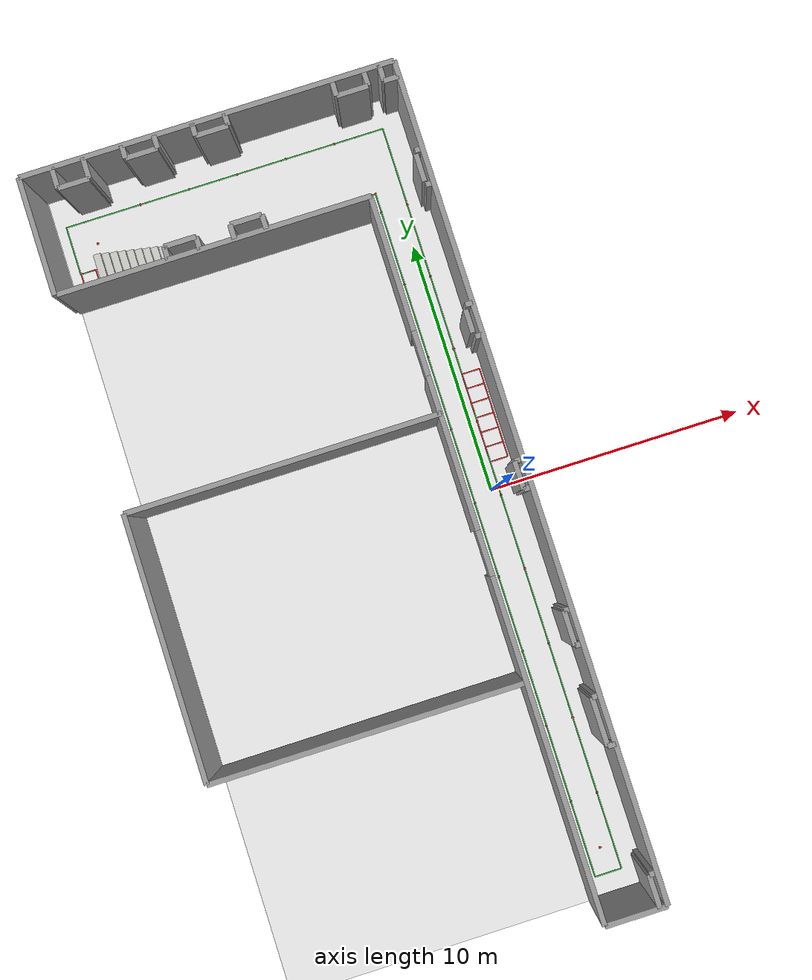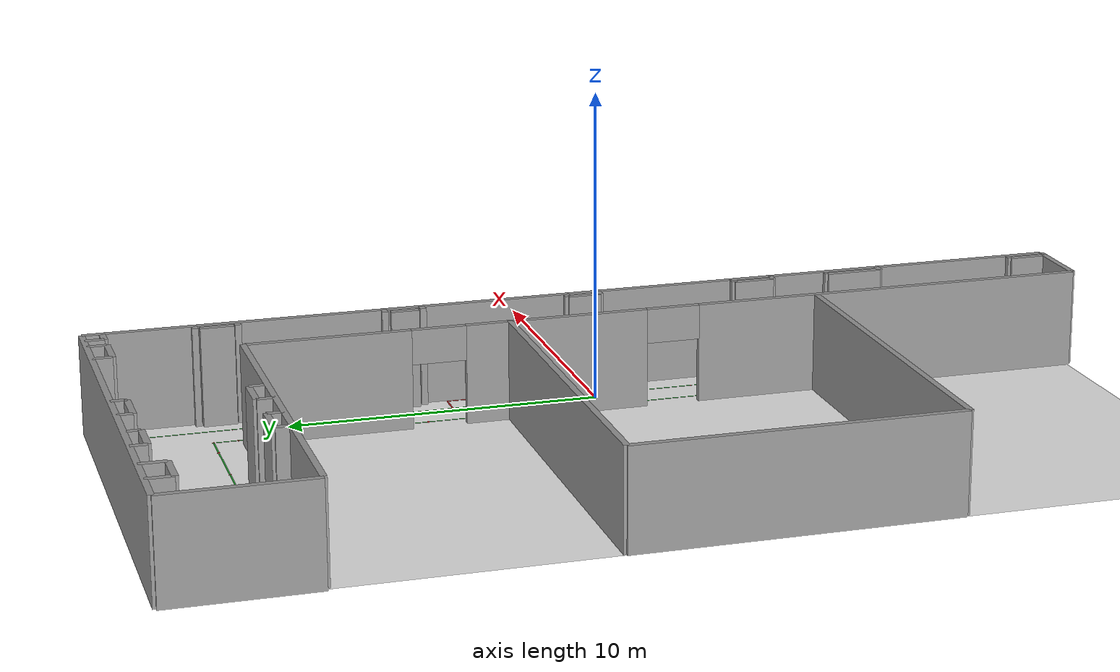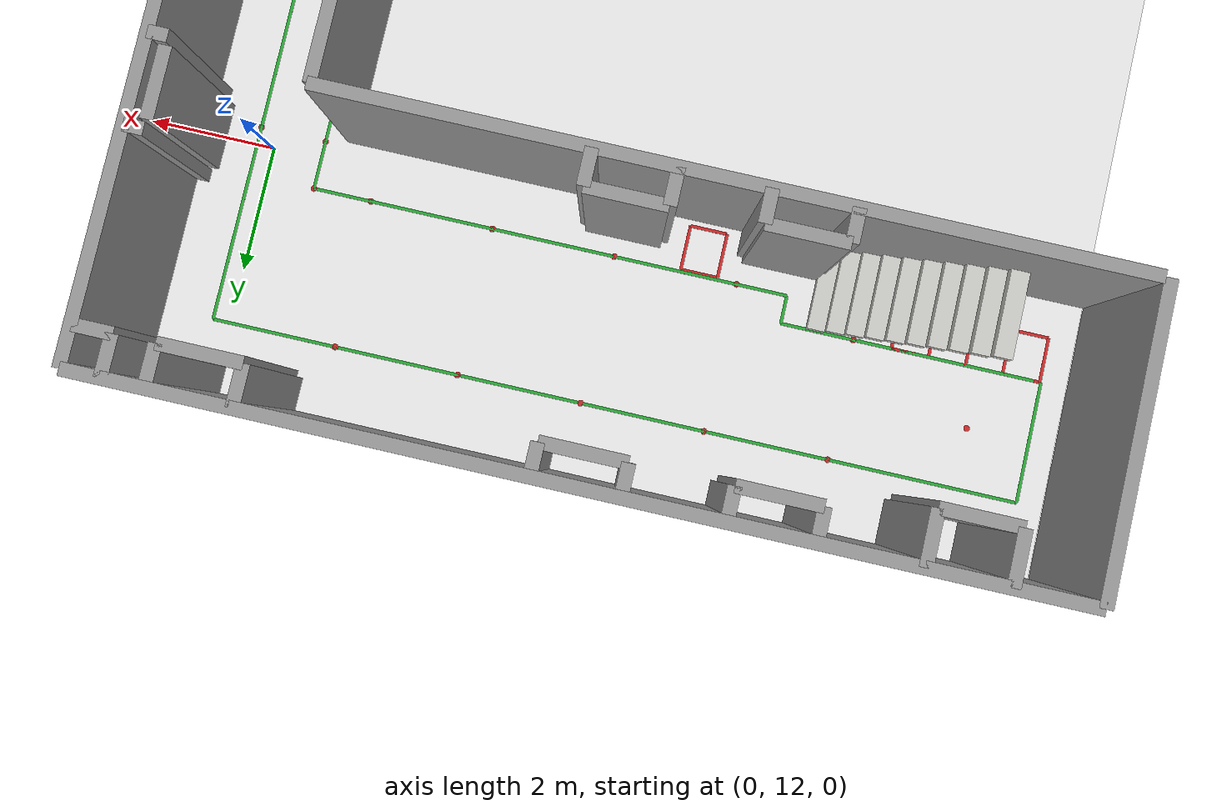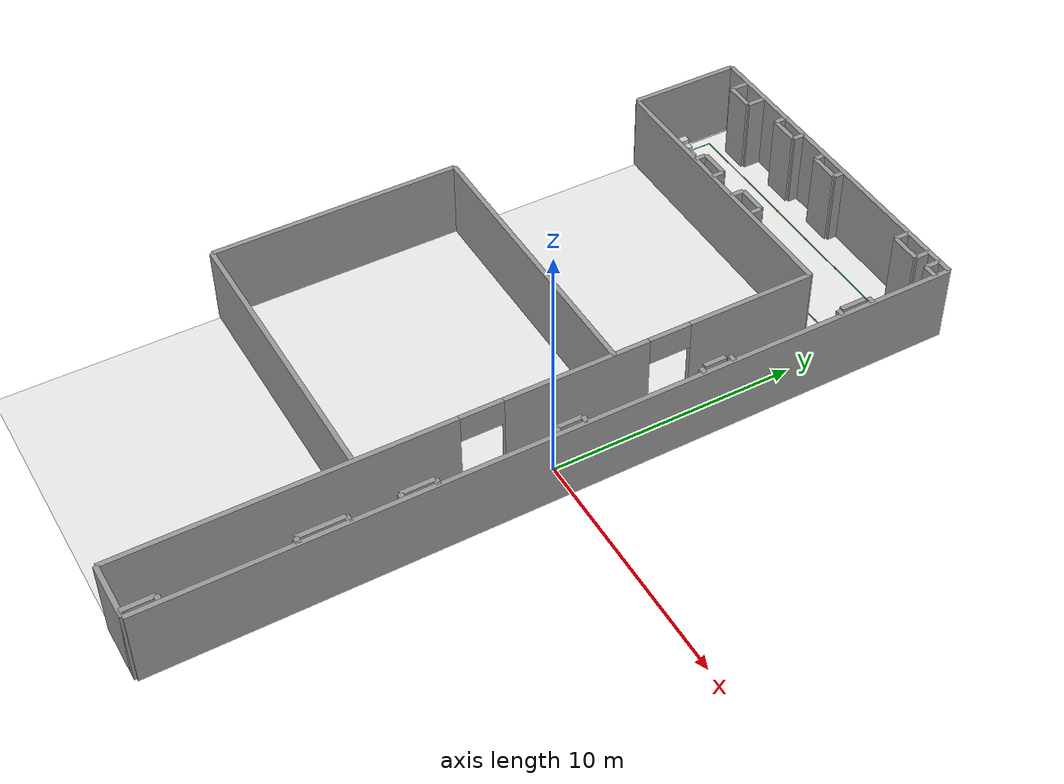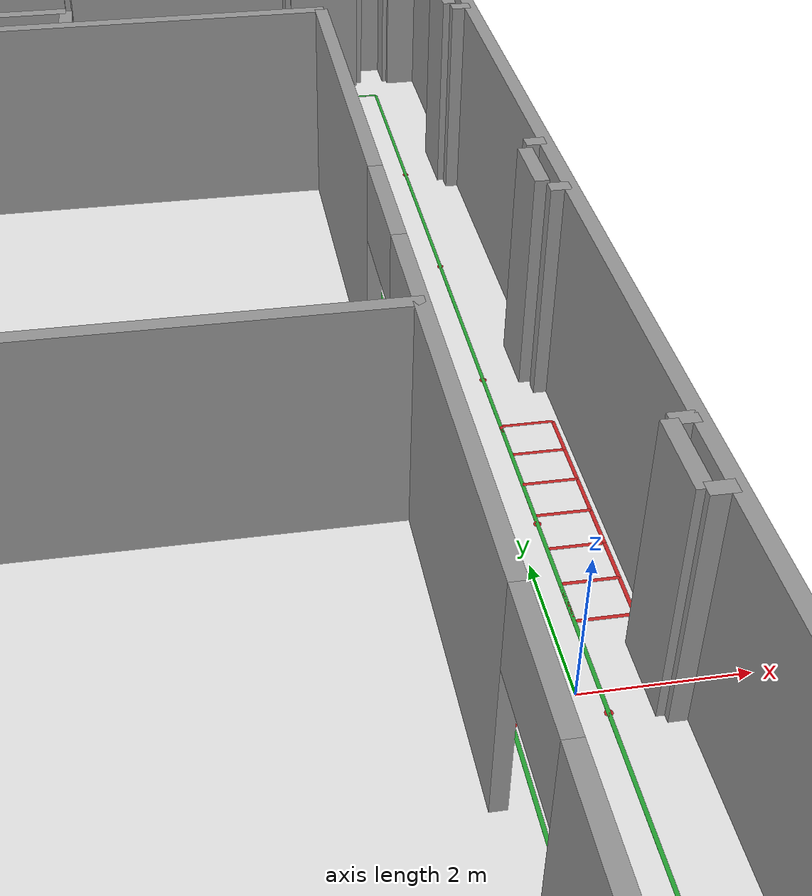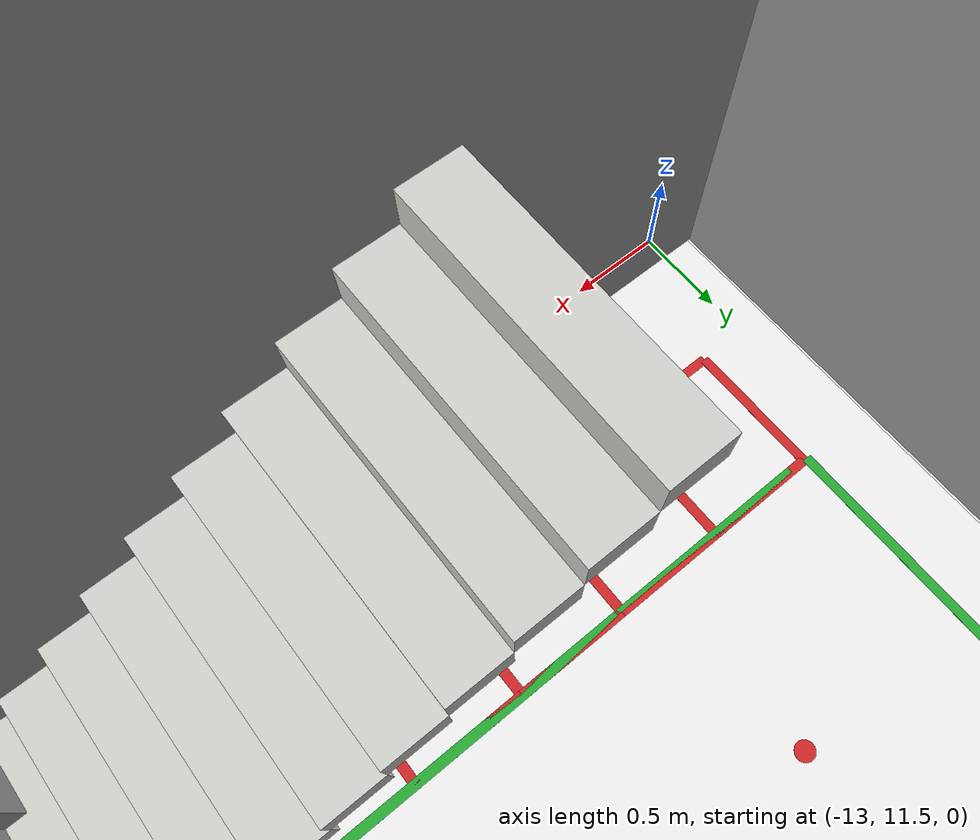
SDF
<?xml version="1.0" ?>
<sdf version="1.6">
  <world name="square_world">

    <spherical_coordinates>
      <surface_model>EARTH_WGS84</surface_model>
      <latitude_deg>51.9906340</latitude_deg>
      <longitude_deg>4.3767889</longitude_deg>
      <elevation>45.110</elevation>
      <heading_deg>180</heading_deg>
    </spherical_coordinates>
    <physics type="ode">
      <max_step_size>0.001</max_step_size>
    </physics>
    <gravity>0 0 -9.8</gravity>
    <gui fullscreen="0">
      <camera name="user_camera">
        <pose>1.49016 -3.72367 3.62379 -2.88294e-17 0.273797 1.4042</pose>
        <view_controller>orbit</view_controller>
      </camera>
    </gui>
    <scene>
      <ambient>0.4 0.4 0.4 1</ambient>
      <background>0.7 0.7 0.7 1</background>
      <shadows>0</shadows>
      <grid>0</grid>
    </scene>
    <model name="floor">
      <static>1</static>
      <pose>-5.99 0 0 0 0 0</pose>
      <link name="link">
        <collision name="collision">
          <geometry>
            <plane>
              <normal>0 0 1</normal>
              <size>14.34 32.2</size>
            </plane>
          </geometry>
          <surface>
            <friction>
              <ode>
                <mu>100</mu>
                <mu2>50</mu2>
              </ode>
            </friction>
            <bounce/>
            <contact>
              <ode/>
            </contact>
          </surface>
          <max_contacts>10</max_contacts>
        </collision>
        <visual name="visual">
          <cast_shadows>0</cast_shadows>
          <geometry>
            <plane>
              <normal>0 0 1</normal>
              <size>14.36 32.2</size>
            </plane>
          </geometry>
          <material>
            <script>
              <name>Gazebo/White</name>
            </script>
          </material>
        </visual>
        <velocity_decay>
          <linear>0</linear>
          <angular>0</angular>
        </velocity_decay>
        <self_collide>0</self_collide>
        <kinematic>0</kinematic>
        <gravity>1</gravity>
      </link>
    </model>

    <model name="wall1">
      <static>true</static>
      <pose>1.18 0 1.6 0 0 -1.5708</pose>
      <link name="wall_link">
        <inertial>
          <mass>10000</mass>
        </inertial>
        <collision name="wall_collision">
          <geometry>
            <box>
              <size>32.2 0.2 3.2</size>
            </box>
          </geometry>
          <surface>
            <contact>
              <collide_bitmask>0x02</collide_bitmask>
            </contact>
          </surface>
        </collision>
        <visual name="wall_visual">
          <geometry>
            <box>
              <size>32.2 0.2 3.2</size>
            </box>
          </geometry>
          <material>
            <script>
              <name>Gazebo/Grey</name>
            </script>
          </material>
        </visual>
      </link>
    </model>
    <model name="wall3">
      <static>true</static>
      <pose>-7.17 11.525 1.6 0 0 0</pose>
      <link name="wall_link">
        <inertial>
          <mass>10000</mass>
        </inertial>
        <collision name="wall_collision">
          <geometry>
            <box>
              <size>12.07 0.2 3.2</size>
            </box>
          </geometry>
          <surface>
            <contact>
              <collide_bitmask>0x02</collide_bitmask>
            </contact>
          </surface>
        </collision>
        <visual name="wall_visual">
          <geometry>
            <box>
              <size>12.07 0.2 3.2</size>
            </box>
          </geometry>
          <material>
            <script>
              <name>Gazebo/Grey</name>
            </script>
          </material>
        </visual>
      </link>
    </model>
   <model name="wall4">
      <static>true</static>
      <pose>0 -16.10 1.6 0 0 0</pose>
      <link name="wall_link">
        <inertial>
          <mass>10000</mass>
        </inertial>
        <collision name="wall_collision">
          <geometry>
            <box>
              <size>2.36 0.2 3.2</size>
            </box>
          </geometry>
          <surface>
            <contact>
              <collide_bitmask>0x02</collide_bitmask>
            </contact>
          </surface>
        </collision>
        <visual name="wall_visual">
          <geometry>
            <box>
              <size>2.36 0.2 3.2</size>
            </box>
          </geometry>
          <material>
            <script>
              <name>Gazebo/Grey</name>
            </script>
          </material>
        </visual>
      </link>
    </model>
 <model name="wall5">
      <static>true</static>
      <pose>-6.05 16.1 1.6 0 0 0</pose>
      <link name="wall_link">
        <inertial>
          <mass>10000</mass>
        </inertial>
        <collision name="wall_collision">
          <geometry>
            <box>
              <size>14.46 0.2 3.2</size>
            </box>
          </geometry>
          <surface>
            <contact>
              <collide_bitmask>0x02</collide_bitmask>
            </contact>
          </surface>
        </collision>
        <visual name="wall_visual">
          <geometry>
            <box>
              <size>14.46 0.2 3.2</size>
            </box>
          </geometry>
          <material>
            <script>
              <name>Gazebo/Grey</name>
            </script>
          </material>
        </visual>
      </link>
    </model>
    <model name="wall6">
      <static>true</static>
      <pose>-13.28 13.8125 1.6 0 0 -1.5708</pose>
      <link name="wall_link">
        <inertial>
          <mass>10000</mass>
        </inertial>
        <collision name="wall_collision">
          <geometry>
            <box>
              <size>4.575 0.2 3.2</size>
            </box>
          </geometry>
          <surface>
            <contact>
              <collide_bitmask>0x02</collide_bitmask>
            </contact>
          </surface>
        </collision>
        <visual name="wall_visual">
          <geometry>
            <box>
              <size>4.575 0.2 3.2</size>
            </box>
          </geometry>
          <material>
            <script>
              <name>Gazebo/Grey</name>
            </script>
          </material>
        </visual>
      </link>
    </model>
<model name="wall7">
      <static>true</static>
      <pose>1.0315 -16.10 1.6 0 0 0</pose>
      <link name="wall_link">
        <inertial>
          <mass>10000</mass>
        </inertial>
        <collision name="wall_collision">
          <geometry>
            <box>
              <size>0.297 0.2 3.2</size>
            </box>
          </geometry>
          <surface>
            <contact>
              <collide_bitmask>0x02</collide_bitmask>
            </contact>
          </surface>
        </collision>
        <visual name="wall_visual">
          <geometry>
            <box>
              <size>0.297 0.2 3.2</size>
            </box>
          </geometry>
          <material>
            <script>
              <name> Gazebo/Grey</name>
            </script>
          </material>
        </visual>
      </link>
    </model>
<model name="wall8">
      <static>true</static>
      <pose>1.0315 -14.86 1.6 0 0 0</pose>
      <link name="wall_link">
        <inertial>
          <mass>10000</mass>
        </inertial>
        <collision name="wall_collision">
          <geometry>
            <box>
              <size>0.297 0.2 3.2</size>
            </box>
          </geometry>
          <surface>
            <contact>
              <collide_bitmask>0x02</collide_bitmask>
            </contact>
          </surface>
        </collision>
        <visual name="wall_visual">
          <geometry>
            <box>
              <size>0.297 0.2 3.2</size>
            </box>
          </geometry>
          <material>
            <script>
              <name> Gazebo/Grey</name>
            </script>
          </material>
        </visual>
      </link>
    </model>
 <model name="wall9">
      <static>true</static>
      <pose>0.883 -15.48 1.6 0 0 -1.5708</pose>
      <link name="wall_link">
        <inertial>
          <mass>10000</mass>
        </inertial>
        <collision name="wall_collision">
          <geometry>
            <box>
              <size>1.24 0.2 3.2</size>
            </box>
          </geometry>
          <surface>
            <contact>
              <collide_bitmask>0x02</collide_bitmask>
            </contact>
          </surface>
        </collision>
        <visual name="wall_visual">
          <geometry>
            <box>
              <size>1.24 0.2 3.2</size>
            </box>
          </geometry>
          <material>
            <script>
              <name> Gazebo/Grey</name>
            </script>
          </material>
        </visual>
      </link>
    </model>
<model name="wall10">
      <static>true</static>
      <pose>1.035 -10.1 1.6 0 0 0</pose>
      <link name="wall_link">
        <inertial>
          <mass>10000</mass>
        </inertial>
        <collision name="wall_collision">
          <geometry>
            <box>
              <size>0.29 0.2 3.2</size>
            </box>
          </geometry>
          <surface>
            <contact>
              <collide_bitmask>0x02</collide_bitmask>
            </contact>
          </surface>
        </collision>
        <visual name="wall_visual">
          <geometry>
            <box>
              <size>0.29 0.2 3.2</size>
            </box>
          </geometry>
          <material>
            <script>
              <name> Gazebo/Grey</name>
            </script>
          </material>
        </visual>
      </link>
    </model>
<model name="wall11">
      <static>true</static>
      <pose>1.035 -8.28 1.6 0 0 0</pose>
      <link name="wall_link">
        <inertial>
          <mass>10000</mass>
        </inertial>
        <collision name="wall_collision">
          <geometry>
            <box>
              <size>0.29 0.2 3.2</size>
            </box>
          </geometry>
          <surface>
            <contact>
              <collide_bitmask>0x02</collide_bitmask>
            </contact>
          </surface>
        </collision>
        <visual name="wall_visual">
          <geometry>
            <box>
              <size>0.29 0.2 3.2</size>
            </box>
          </geometry>
          <material>
            <script>
              <name> Gazebo/Grey</name>
            </script>
          </material>
        </visual>
      </link>
    </model>
 <model name="wall12">
      <static>true</static>
      <pose>0.89 -9.19 1.6 0 0 -1.5708</pose>
      <link name="wall_link">
        <inertial>
          <mass>10000</mass>
        </inertial>
        <collision name="wall_collision">
          <geometry>
            <box>
              <size>1.82 0.2 3.2</size>
            </box>
          </geometry>
          <surface>
            <contact>
              <collide_bitmask>0x02</collide_bitmask>
            </contact>
          </surface>
        </collision>
        <visual name="wall_visual">
          <geometry>
            <box>
              <size>1.82 0.2 3.2</size>
            </box>
          </geometry>
          <material>
            <script>
              <name> Gazebo/Grey</name>
            </script>
          </material>
        </visual>
      </link>
    </model>
<model name="wall13">
      <static>true</static>
      <pose>1.0365 -6.34 1.6 0 0 0</pose>
      <link name="wall_link">
        <inertial>
          <mass>10000</mass>
        </inertial>
        <collision name="wall_collision">
          <geometry>
            <box>
              <size>0.287 0.2 3.2</size>
            </box>
          </geometry>
          <surface>
            <contact>
              <collide_bitmask>0x02</collide_bitmask>
            </contact>
          </surface>
        </collision>
        <visual name="wall_visual">
          <geometry>
            <box>
              <size>0.287 0.2 3.2</size>
            </box>
          </geometry>
          <material>
            <script>
              <name> Gazebo/Grey</name>
            </script>
          </material>
        </visual>
      </link>
    </model>
<model name="wall14">
      <static>true</static>
      <pose>1.0365 -5.03 1.6 0 0 0</pose>
      <link name="wall_link">
        <inertial>
          <mass>10000</mass>
        </inertial>
        <collision name="wall_collision">
          <geometry>
            <box>
              <size>0.287 0.2 3.2</size>
            </box>
          </geometry>
          <surface>
            <contact>
              <collide_bitmask>0x02</collide_bitmask>
            </contact>
          </surface>
        </collision>
        <visual name="wall_visual">
          <geometry>
            <box>
              <size>0.287 0.2 3.2</size>
            </box>
          </geometry>
          <material>
            <script>
              <name> Gazebo/Grey</name>
            </script>
          </material>
        </visual>
      </link>
    </model>
 <model name="wall15">
      <static>true</static>
      <pose>0.893 -5.685 1.6 0 0 -1.5708</pose>
      <link name="wall_link">
        <inertial>
          <mass>10000</mass>
        </inertial>
        <collision name="wall_collision">
          <geometry>
            <box>
              <size>1.31 0.2 3.2</size>
            </box>
          </geometry>
          <surface>
            <contact>
              <collide_bitmask>0x02</collide_bitmask>
            </contact>
          </surface>
        </collision>
        <visual name="wall_visual">
          <geometry>
            <box>
              <size>1.31 0.2 3.2</size>
            </box>
          </geometry>
          <material>
            <script>
              <name> Gazebo/Grey</name>
            </script>
          </material>
        </visual>
      </link>
    </model>
<model name="wall16">
      <static>true</static>
      <pose>1.0195 -0.42 1.6 0 0 0</pose>
      <link name="wall_link">
        <inertial>
          <mass>10000</mass>
        </inertial>
        <collision name="wall_collision">
          <geometry>
            <box>
              <size>0.321 0.2 3.2</size>
            </box>
          </geometry>
          <surface>
            <contact>
              <collide_bitmask>0x02</collide_bitmask>
            </contact>
          </surface>
        </collision>
        <visual name="wall_visual">
          <geometry>
            <box>
              <size>0.321 0.2 3.2</size>
            </box>
          </geometry>
          <material>
            <script>
              <name> Gazebo/Grey</name>
            </script>
          </material>
        </visual>
      </link>
    </model>
<model name="wall17">
      <static>true</static>
      <pose>1.0195 0.65 1.6 0 0 0</pose>
      <link name="wall_link">
        <inertial>
          <mass>10000</mass>
        </inertial>
        <collision name="wall_collision">
          <geometry>
            <box>
              <size>0.321 0.2 3.2</size>
            </box>
          </geometry>
          <surface>
            <contact>
              <collide_bitmask>0x02</collide_bitmask>
            </contact>
          </surface>
        </collision>
        <visual name="wall_visual">
          <geometry>
            <box>
              <size>0.321 0.2 3.2</size>
            </box>
          </geometry>
          <material>
            <script>
              <name> Gazebo/Grey</name>
            </script>
          </material>
        </visual>
      </link>
    </model>
 <model name="wall18">
      <static>true</static>
      <pose>0.859 0.115 1.6 0 0 -1.5708</pose>
      <link name="wall_link">
        <inertial>
          <mass>10000</mass>
        </inertial>
        <collision name="wall_collision">
          <geometry>
            <box>
              <size>1.07 0.2 3.2</size>
            </box>
          </geometry>
          <surface>
            <contact>
              <collide_bitmask>0x02</collide_bitmask>
            </contact>
          </surface>
        </collision>
        <visual name="wall_visual">
          <geometry>
            <box>
              <size>1.07 0.2 3.2</size>
            </box>
          </geometry>
          <material>
            <script>
              <name> Gazebo/Grey</name>
            </script>
          </material>
        </visual>
      </link>
    </model>
<model name="wall19">
      <static>true</static>
      <pose>1.04 5.41 1.6 0 0 0</pose>
      <link name="wall_link">
        <inertial>
          <mass>10000</mass>
        </inertial>
        <collision name="wall_collision">
          <geometry>
            <box>
              <size>0.28 0.2 3.2</size>
            </box>
          </geometry>
          <surface>
            <contact>
              <collide_bitmask>0x02</collide_bitmask>
            </contact>
          </surface>
        </collision>
        <visual name="wall_visual">
          <geometry>
            <box>
              <size>0.28 0.2 3.2</size>
            </box>
          </geometry>
          <material>
            <script>
              <name> Gazebo/Grey</name>
            </script>
          </material>
        </visual>
      </link>
    </model>
<model name="wall20">
      <static>true</static>
      <pose>1.04 6.64 1.6 0 0 0</pose>
      <link name="wall_link">
        <inertial>
          <mass>10000</mass>
        </inertial>
        <collision name="wall_collision">
          <geometry>
            <box>
              <size>0.28 0.2 3.2</size>
            </box>
          </geometry>
          <surface>
            <contact>
              <collide_bitmask>0x02</collide_bitmask>
            </contact>
          </surface>
        </collision>
        <visual name="wall_visual">
          <geometry>
            <box>
              <size>0.28 0.2 3.2</size>
            </box>
          </geometry>
          <material>
            <script>
              <name> Gazebo/Grey</name>
            </script>
          </material>
        </visual>
      </link>
    </model>
 <model name="wall21">
      <static>true</static>
      <pose>0.859 6.025 1.6 0 0 -1.5708</pose>
      <link name="wall_link">
        <inertial>
          <mass>10000</mass>
        </inertial>
        <collision name="wall_collision">
          <geometry>
            <box>
              <size>0.9 0.2 3.2</size>
            </box>
          </geometry>
          <surface>
            <contact>
              <collide_bitmask>0x02</collide_bitmask>
            </contact>
          </surface>
        </collision>
        <visual name="wall_visual">
          <geometry>
            <box>
              <size>0.9 0.2 3.2</size>
            </box>
          </geometry>
          <material>
            <script>
              <name> Gazebo/Grey</name>
            </script>
          </material>
        </visual>
      </link>
    </model>
<model name="wall22">
      <static>true</static>
      <pose>1.0315 11.31 1.6 0 0 0</pose>
      <link name="wall_link">
        <inertial>
          <mass>10000</mass>
        </inertial>
        <collision name="wall_collision">
          <geometry>
            <box>
              <size>0.297 0.2 3.2</size>
            </box>
          </geometry>
          <surface>
            <contact>
              <collide_bitmask>0x02</collide_bitmask>
            </contact>
          </surface>
        </collision>
        <visual name="wall_visual">
          <geometry>
            <box>
              <size>0.297 0.2 3.2</size>
            </box>
          </geometry>
          <material>
            <script>
              <name> Gazebo/Grey</name>
            </script>
          </material>
        </visual>
      </link>
    </model>
<model name="wall23">
      <static>true</static>
      <pose>1.0315 12.65 1.6 0 0 0</pose>
      <link name="wall_link">
        <inertial>
          <mass>10000</mass>
        </inertial>
        <collision name="wall_collision">
          <geometry>
            <box>
              <size>0.297 0.2 3.2</size>
            </box>
          </geometry>
          <surface>
            <contact>
              <collide_bitmask>0x02</collide_bitmask>
            </contact>
          </surface>
        </collision>
        <visual name="wall_visual">
          <geometry>
            <box>
              <size>0.297 0.2 3.2</size>
            </box>
          </geometry>
          <material>
            <script>
              <name> Gazebo/Grey</name>
            </script>
          </material>
        </visual>
      </link>
    </model>
 <model name="wall24">
      <static>true</static>
      <pose>0.883 11.98 1.6 0 0 -1.5708</pose>
      <link name="wall_link">
        <inertial>
          <mass>10000</mass>
        </inertial>
        <collision name="wall_collision">
          <geometry>
            <box>
              <size>1.07 0.2 3.2</size>
            </box>
          </geometry>
          <surface>
            <contact>
              <collide_bitmask>0x02</collide_bitmask>
            </contact>
          </surface>
        </collision>
        <visual name="wall_visual">
          <geometry>
            <box>
              <size>1.07 0.2 3.2</size>
            </box>
          </geometry>
          <material>
            <script>
              <name> Gazebo/Grey</name>
            </script>
          </material>
        </visual>
      </link>
    </model>
<model name="wall25">
      <static>true</static>
      <pose>0.87 15.48 1.6 0 0 0</pose>
      <link name="wall_link">
        <inertial>
          <mass>10000</mass>
        </inertial>
        <collision name="wall_collision">
          <geometry>
            <box>
              <size>0.58 0.2 3.2</size>
            </box>
          </geometry>
          <surface>
            <contact>
              <collide_bitmask>0x02</collide_bitmask>
            </contact>
          </surface>
        </collision>
        <visual name="wall_visual">
          <geometry>
            <box>
              <size>0.58 0.2 3.2</size>
            </box>
          </geometry>
          <material>
            <script>
              <name> Gazebo/Grey</name>
            </script>
          </material>
        </visual>
      </link>
    </model>
 <model name="wall26">
      <static>true</static>
      <pose>0.6 15.79 1.6 0 0 -1.5708</pose>
      <link name="wall_link">
        <inertial>
          <mass>10000</mass>
        </inertial>
        <collision name="wall_collision">
          <geometry>
            <box>
              <size>0.62 0.2 3.2</size>
            </box>
          </geometry>
          <surface>
            <contact>
              <collide_bitmask>0x02</collide_bitmask>
            </contact>
          </surface>
        </collision>
        <visual name="wall_visual">
          <geometry>
            <box>
              <size>0.62 0.2 3.2</size>
            </box>
          </geometry>
          <material>
            <script>
              <name> Gazebo/Grey</name>
            </script>
          </material>
        </visual>
      </link>
    </model>
<model name="wall27">
      <static>true</static>
      <pose>-0.01 15.787 1.6 0 0 -1.5708</pose>
      <link name="wall_link">
        <inertial>
          <mass>10000</mass>
        </inertial>
        <collision name="wall_collision">
          <geometry>
            <box>
              <size>0.626 0.2 3.2</size>
            </box>
          </geometry>
          <surface>
            <contact>
              <collide_bitmask>0x02</collide_bitmask>
            </contact>
          </surface>
        </collision>
        <visual name="wall_visual">
          <geometry>
            <box>
              <size>0.626 0.2 3.2</size>
            </box>
          </geometry>
          <material>
            <script>
              <name> Gazebo/Grey</name>
            </script>
          </material>
        </visual>
      </link>
    </model>
<model name="wall28">
      <static>true</static>
      <pose>-1.24 15.787 1.6 0 0 -1.5708</pose>
      <link name="wall_link">
        <inertial>
          <mass>10000</mass>
        </inertial>
        <collision name="wall_collision">
          <geometry>
            <box>
              <size>0.626 0.2 3.2</size>
            </box>
          </geometry>
          <surface>
            <contact>
              <collide_bitmask>0x02</collide_bitmask>
            </contact>
          </surface>
        </collision>
        <visual name="wall_visual">
          <geometry>
            <box>
              <size>0.626 0.2 3.2</size>
            </box>
          </geometry>
          <material>
            <script>
              <name> Gazebo/Grey</name>
            </script>
          </material>
        </visual>
      </link>
    </model>
 <model name="wall29">
      <static>true</static>
      <pose>-0.625 15.474 1.6 0 0 0</pose>
      <link name="wall_link">
        <inertial>
          <mass>10000</mass>
        </inertial>
        <collision name="wall_collision">
          <geometry>
            <box>
              <size>1.23 0.2 3.2</size>
            </box>
          </geometry>
          <surface>
            <contact>
              <collide_bitmask>0x02</collide_bitmask>
            </contact>
          </surface>
        </collision>
        <visual name="wall_visual">
          <geometry>
            <box>
              <size>1.23 0.2 3.2</size>
            </box>
          </geometry>
          <material>
            <script>
              <name> Gazebo/Grey</name>
            </script>
          </material>
        </visual>
      </link>
    </model>
<model name="wall30">
      <static>true</static>
      <pose>-5.37 15.86 1.6 0 0 -1.5708</pose>
      <link name="wall_link">
        <inertial>
          <mass>10000</mass>
        </inertial>
        <collision name="wall_collision">
          <geometry>
            <box>
              <size>0.48 0.2 3.2</size>
            </box>
          </geometry>
          <surface>
            <contact>
              <collide_bitmask>0x02</collide_bitmask>
            </contact>
          </surface>
        </collision>
        <visual name="wall_visual">
          <geometry>
            <box>
              <size>0.48 0.2 3.2</size>
            </box>
          </geometry>
          <material>
            <script>
              <name> Gazebo/Grey</name>
            </script>
          </material>
        </visual>
      </link>
    </model>
<model name="wall31">
      <static>true</static>
      <pose>-6.63 15.86 1.6 0 0 -1.5708</pose>
      <link name="wall_link">
        <inertial>
          <mass>10000</mass>
        </inertial>
        <collision name="wall_collision">
          <geometry>
            <box>
              <size>0.48 0.2 3.2</size>
            </box>
          </geometry>
          <surface>
            <contact>
              <collide_bitmask>0x02</collide_bitmask>
            </contact>
          </surface>
        </collision>
        <visual name="wall_visual">
          <geometry>
            <box>
              <size>0.48 0.2 3.2</size>
            </box>
          </geometry>
          <material>
            <script>
              <name> Gazebo/Grey</name>
            </script>
          </material>
        </visual>
      </link>
    </model>
 <model name="wall32">
      <static>true</static>
      <pose>-6 15.62 1.6 0 0 0</pose>
      <link name="wall_link">
        <inertial>
          <mass>10000</mass>
        </inertial>
        <collision name="wall_collision">
          <geometry>
            <box>
              <size>1.26 0.2 3.2</size>
            </box>
          </geometry>
          <surface>
            <contact>
              <collide_bitmask>0x02</collide_bitmask>
            </contact>
          </surface>
        </collision>
        <visual name="wall_visual">
          <geometry>
            <box>
              <size>1.26 0.2 3.2</size>
            </box>
          </geometry>
          <material>
            <script>
              <name> Gazebo/Grey</name>
            </script>
          </material>
        </visual>
      </link>
    </model>
<model name="wall33">
      <static>true</static>
      <pose>-8.09 15.85 1.6 0 0 -1.5708</pose>
      <link name="wall_link">
        <inertial>
          <mass>10000</mass>
        </inertial>
        <collision name="wall_collision">
          <geometry>
            <box>
              <size>0.50 0.2 3.2</size>
            </box>
          </geometry>
          <surface>
            <contact>
              <collide_bitmask>0x02</collide_bitmask>
            </contact>
          </surface>
        </collision>
        <visual name="wall_visual">
          <geometry>
            <box>
              <size>0.50 0.2 3.2</size>
            </box>
          </geometry>
          <material>
            <script>
              <name> Gazebo/Grey</name>
            </script>
          </material>
        </visual>
      </link>
    </model>
<model name="wall34">
      <static>true</static>
      <pose>-9.33 15.85 1.6 0 0 -1.5708</pose>
      <link name="wall_link">
        <inertial>
          <mass>10000</mass>
        </inertial>
        <collision name="wall_collision">
          <geometry>
            <box>
              <size>0.50 0.2 3.2</size>
            </box>
          </geometry>
          <surface>
            <contact>
              <collide_bitmask>0x02</collide_bitmask>
            </contact>
          </surface>
        </collision>
        <visual name="wall_visual">
          <geometry>
            <box>
              <size>0.50 0.2 3.2</size>
            </box>
          </geometry>
          <material>
            <script>
              <name> Gazebo/Grey</name>
            </script>
          </material>
        </visual>
      </link>
    </model>
 <model name="wall35">
      <static>true</static>
      <pose>-8.71 15.6 1.6 0 0 0</pose>
      <link name="wall_link">
        <inertial>
          <mass>10000</mass>
        </inertial>
        <collision name="wall_collision">
          <geometry>
            <box>
              <size>1.24 0.2 3.2</size>
            </box>
          </geometry>
          <surface>
            <contact>
              <collide_bitmask>0x02</collide_bitmask>
            </contact>
          </surface>
        </collision>
        <visual name="wall_visual">
          <geometry>
            <box>
              <size>1.24 0.2 3.2</size>
            </box>
          </geometry>
          <material>
            <script>
              <name> Gazebo/Grey</name>
            </script>
          </material>
        </visual>
      </link>
    </model>
<model name="wall36">
      <static>true</static>
      <pose>-10.82 15.69 1.6 0 0 -1.5708</pose>
      <link name="wall_link">
        <inertial>
          <mass>10000</mass>
        </inertial>
        <collision name="wall_collision">
          <geometry>
            <box>
              <size>0.82 0.2 3.2</size>
            </box>
          </geometry>
          <surface>
            <contact>
              <collide_bitmask>0x02</collide_bitmask>
            </contact>
          </surface>
        </collision>
        <visual name="wall_visual">
          <geometry>
            <box>
              <size>0.82 0.2 3.2</size>
            </box>
          </geometry>
          <material>
            <script>
              <name> Gazebo/Grey</name>
            </script>
          </material>
        </visual>
      </link>
    </model>
<model name="wall37">
      <static>true</static>
      <pose>-12.02 15.69 1.6 0 0 -1.5708</pose>
      <link name="wall_link">
        <inertial>
          <mass>10000</mass>
        </inertial>
        <collision name="wall_collision">
          <geometry>
            <box>
              <size>0.82 0.2 3.2</size>
            </box>
          </geometry>
          <surface>
            <contact>
              <collide_bitmask>0x02</collide_bitmask>
            </contact>
          </surface>
        </collision>
        <visual name="wall_visual">
          <geometry>
            <box>
              <size>0.82 0.2 3.2</size>
            </box>
          </geometry>
          <material>
            <script>
              <name> Gazebo/Grey</name>
            </script>
          </material>
        </visual>
      </link>
    </model>
 <model name="wall38">
      <static>true</static>
      <pose>-11.42 15.28 1.6 0 0 0</pose>
      <link name="wall_link">
        <inertial>
          <mass>10000</mass>
        </inertial>
        <collision name="wall_collision">
          <geometry>
            <box>
              <size>1.20 0.2 3.2</size>
            </box>
          </geometry>
          <surface>
            <contact>
              <collide_bitmask>0x02</collide_bitmask>
            </contact>
          </surface>
        </collision>
        <visual name="wall_visual">
          <geometry>
            <box>
              <size>1.20 0.2 3.2</size>
            </box>
          </geometry>
          <material>
            <script>
              <name> Gazebo/Grey</name>
            </script>
          </material>
        </visual>
      </link>
    </model>
<model name="wall39">
      <static>true</static>
      <pose>-5.18 11.8025 1.6 0 0 -1.5708</pose>
      <link name="wall_link">
        <inertial>
          <mass>10000</mass>
        </inertial>
        <collision name="wall_collision">
          <geometry>
            <box>
              <size>0.555 0.2 3.2</size>
            </box>
          </geometry>
          <surface>
            <contact>
              <collide_bitmask>0x02</collide_bitmask>
            </contact>
          </surface>
        </collision>
        <visual name="wall_visual">
          <geometry>
            <box>
              <size>0.555 0.2 3.2</size>
            </box>
          </geometry>
          <material>
            <script>
              <name> Gazebo/Grey</name>
            </script>
          </material>
        </visual>
      </link>
    </model>
<model name="wall40">
      <static>true</static>
      <pose>-6.4 11.8025 1.6 0 0 -1.5708</pose>
      <link name="wall_link">
        <inertial>
          <mass>10000</mass>
        </inertial>
        <collision name="wall_collision">
          <geometry>
            <box>
              <size>0.555 0.2 3.2</size>
            </box>
          </geometry>
          <surface>
            <contact>
              <collide_bitmask>0x02</collide_bitmask>
            </contact>
          </surface>
        </collision>
        <visual name="wall_visual">
          <geometry>
            <box>
              <size>0.555 0.2 3.2</size>
            </box>
          </geometry>
          <material>
            <script>
              <name> Gazebo/Grey</name>
            </script>
          </material>
        </visual>
      </link>
    </model>
 <model name="wall41">
      <static>true</static>
      <pose>-5.79 12.08 1.6 0 0 0</pose>
      <link name="wall_link">
        <inertial>
          <mass>10000</mass>
        </inertial>
        <collision name="wall_collision">
          <geometry>
            <box>
              <size>1.22 0.2 3.2</size>
            </box>
          </geometry>
          <surface>
            <contact>
              <collide_bitmask>0x02</collide_bitmask>
            </contact>
          </surface>
        </collision>
        <visual name="wall_visual">
          <geometry>
            <box>
              <size>1.22 0.2 3.2</size>
            </box>
          </geometry>
          <material>
            <script>
              <name> Gazebo/Grey</name>
            </script>
          </material>
        </visual>
      </link>
    </model>
<model name="wall42">
      <static>true</static>
      <pose>-7.72 11.7775 1.6 0 0 -1.5708</pose>
      <link name="wall_link">
        <inertial>
          <mass>10000</mass>
        </inertial>
        <collision name="wall_collision">
          <geometry>
            <box>
              <size>0.505 0.2 3.2</size>
            </box>
          </geometry>
          <surface>
            <contact>
              <collide_bitmask>0x02</collide_bitmask>
            </contact>
          </surface>
        </collision>
        <visual name="wall_visual">
          <geometry>
            <box>
              <size>0.505 0.2 3.2</size>
            </box>
          </geometry>
          <material>
            <script>
              <name> Gazebo/Grey</name>
            </script>
          </material>
        </visual>
      </link>
    </model>
<model name="wall43">
      <static>true</static>
      <pose>-8.94 11.7775 1.6 0 0 -1.5708</pose>
      <link name="wall_link">
        <inertial>
          <mass>10000</mass>
        </inertial>
        <collision name="wall_collision">
          <geometry>
            <box>
              <size>0.505 0.2 3.2</size>
            </box>
          </geometry>
          <surface>
            <contact>
              <collide_bitmask>0x02</collide_bitmask>
            </contact>
          </surface>
        </collision>
        <visual name="wall_visual">
          <geometry>
            <box>
              <size>0.505 0.2 3.2</size>
            </box>
          </geometry>
          <material>
            <script>
              <name> Gazebo/Grey</name>
            </script>
          </material>
        </visual>
      </link>
    </model>
 <model name="wall44">
      <static>true</static>
      <pose>-8.33 12.03 1.6 0 0 0</pose>
      <link name="wall_link">
        <inertial>
          <mass>10000</mass>
        </inertial>
        <collision name="wall_collision">
          <geometry>
            <box>
              <size>1.22 0.2 3.2</size>
            </box>
          </geometry>
          <surface>
            <contact>
              <collide_bitmask>0x02</collide_bitmask>
            </contact>
          </surface>
        </collision>
        <visual name="wall_visual">
          <geometry>
            <box>
              <size>1.22 0.2 3.2</size>
            </box>
          </geometry>
          <material>
            <script>
              <name> Gazebo/Grey</name>
            </script>
          </material>
        </visual>
      </link>
    </model>
  <model name="wall45">
      <static>true</static>
      <pose>-1.18 -9.58 1.6 0 0 -1.5708</pose>
      <link name="wall_link">
        <inertial>
          <mass>10000</mass>
        </inertial>
        <collision name="wall_collision">
          <geometry>
            <box>
              <size>13.04 0.2 3.2</size>
            </box>
          </geometry>
          <surface>
            <contact>
              <collide_bitmask>0x02</collide_bitmask>
            </contact>
          </surface>
        </collision>
        <visual name="wall_visual">
          <geometry>
            <box>
              <size>13.04 0.2 3.2</size>
            </box>
          </geometry>
          <material>
            <script>
              <name>Gazebo/Grey</name>
            </script>
          </material>
        </visual>
      </link>
    </model>
  <model name="wall46">
      <static>true</static>
      <pose>-1.18 1.62 1.6 0 0 -1.5708</pose>
      <link name="wall_link">
        <inertial>
          <mass>10000</mass>
        </inertial>
        <collision name="wall_collision">
          <geometry>
            <box>
              <size>5.9 0.2 3.2</size>
            </box>
          </geometry>
          <surface>
            <contact>
              <collide_bitmask>0x02</collide_bitmask>
            </contact>
          </surface>
        </collision>
        <visual name="wall_visual">
          <geometry>
            <box>
              <size>5.9 0.2 3.2</size>
            </box>
          </geometry>
          <material>
            <script>
              <name>Gazebo/Grey</name>
            </script>
          </material>
        </visual>
      </link>
    </model>
  <model name="wall47">
      <static>true</static>
      <pose>-1.18 8.91 1.6 0 0 -1.5708</pose>
      <link name="wall_link">
        <inertial>
          <mass>10000</mass>
        </inertial>
        <collision name="wall_collision">
          <geometry>
            <box>
              <size>5.22 0.2 3.2</size>
            </box>
          </geometry>
          <surface>
            <contact>
              <collide_bitmask>0x02</collide_bitmask>
            </contact>
          </surface>
        </collision>
        <visual name="wall_visual">
          <geometry>
            <box>
              <size>5.22 0.2 3.2</size>
            </box>
          </geometry>
          <material>
            <script>
              <name>Gazebo/Grey</name>
            </script>
          </material>
        </visual>
      </link>
    </model>
   <model name="wall48">
      <static>true</static>
      <pose>-7.17 3.12 1.6 0 0 0</pose>
      <link name="wall_link">
        <inertial>
          <mass>10000</mass>
        </inertial>
        <collision name="wall_collision">
          <geometry>
            <box>
              <size>12.07 0.2 3.2</size>
            </box>
          </geometry>
          <surface>
            <contact>
              <collide_bitmask>0x02</collide_bitmask>
            </contact>
          </surface>
        </collision>
        <visual name="wall_visual">
          <geometry>
            <box>
              <size>12.07 0.2 3.2</size>
            </box>
          </geometry>
          <material>
            <script>
              <name>Gazebo/Grey</name>
            </script>
          </material>
        </visual>
      </link>
    </model>
  <model name="wall49">
      <static>true</static>
      <pose>-13.205 -1.97 1.6 0 0 -1.5708</pose>
      <link name="wall_link">
        <inertial>
          <mass>10000</mass>
        </inertial>
        <collision name="wall_collision">
          <geometry>
            <box>
              <size>10.18 0.2 3.2</size>
            </box>
          </geometry>
          <surface>
            <contact>
              <collide_bitmask>0x02</collide_bitmask>
            </contact>
          </surface>
        </collision>
        <visual name="wall_visual">
          <geometry>
            <box>
              <size>10.18 0.2 3.2</size>
            </box>
          </geometry>
          <material>
            <script>
              <name>Gazebo/Grey</name>
            </script>
          </material>
        </visual>
      </link>
    </model>
<model name="wall50">
      <static>true</static>
      <pose>-7.17 -7.06 1.6 0 0 0</pose>
      <link name="wall_link">
        <inertial>
          <mass>10000</mass>
        </inertial>
        <collision name="wall_collision">
          <geometry>
            <box>
              <size>12.07 0.2 3.2</size>
            </box>
          </geometry>
          <surface>
            <contact>
              <collide_bitmask>0x02</collide_bitmask>
            </contact>
          </surface>
        </collision>
        <visual name="wall_visual">
          <geometry>
            <box>
              <size>12.07 0.2 3.2</size>
            </box>
          </geometry>
          <material>
            <script>
              <name>Gazebo/Grey</name>
            </script>
          </material>
        </visual>
      </link>
    </model>
  <model name='Stairs'>
    <pose frame=''>-10.345 12.23 0 0 -0 0</pose>
    <link name='Stairs_1'>
      <visual name='Stairs_1_Visual_0'>
        <pose frame=''>1.2645 0 0.0935 0 0 -1.5708</pose>
        <geometry>
          <box>
            <size>1.41 0.281 0.187</size>
          </box>
        </geometry>
        <material>
          <script>
            <uri>file://media/materials/scripts/gazebo.material</uri>
            <name>Gazebo/CeilingTiled</name>
          </script>
          <ambient>0.760784 0.662745 0.627451 1</ambient>
        </material>
      </visual>
      <collision name='Stairs_1_Collision_0'>
        <geometry>
          <box>
            <size>1.41 0.281 0.187</size>
          </box>
        </geometry>
        <pose frame=''>1.2645 0 0.0935 0 0 -1.5708</pose>
      </collision>
      <visual name='Stairs_1_Visual_1'>
        <pose frame=''>0.9835 0 0.2805 0 0 -1.5708</pose>
        <geometry>
          <box>
            <size>1.41 0.281 0.187</size>
          </box>
        </geometry>
        <material>
          <script>
            <uri>file://media/materials/scripts/gazebo.material</uri>
            <name>Gazebo/CeilingTiled</name>
          </script>
          <ambient>0.760784 0.662745 0.627451 1</ambient>
        </material>
      </visual>
      <collision name='Stairs_1_Collision_1'>
        <geometry>
          <box>
            <size>1.41 0.281 0.187</size>
          </box>
        </geometry>
        <pose frame=''>0.9835 0 0.2805 0 0 -1.5708</pose>
      </collision>
      <visual name='Stairs_1_Visual_2'>
        <pose frame=''>0.7025 0 0.4675 0 0 -1.5708</pose>
        <geometry>
          <box>
            <size>1.41 0.281 0.187</size>
          </box>
        </geometry>
        <material>
          <script>
            <uri>file://media/materials/scripts/gazebo.material</uri>
            <name>Gazebo/CeilingTiled</name>
          </script>
          <ambient>0.760784 0.662745 0.627451 1</ambient>
        </material>
      </visual>
      <collision name='Stairs_1_Collision_2'>
        <geometry>
          <box>
            <size>1.41 0.281 0.187</size>
          </box>
        </geometry>
        <pose frame=''>0.7025 0 0.4675 0 0 -1.5708</pose>
      </collision>
      <visual name='Stairs_1_Visual_3'>
        <pose frame=''>0.4215 0 0.6545 0 0 -1.5708</pose>
        <geometry>
          <box>
            <size>1.41 0.281 0.187</size>
          </box>
        </geometry>
        <material>
          <script>
            <uri>file://media/materials/scripts/gazebo.material</uri>
            <name>Gazebo/CeilingTiled</name>
          </script>
          <ambient>0.760784 0.662745 0.627451 1</ambient>
        </material>
      </visual>
      <collision name='Stairs_1_Collision_3'>
        <geometry>
          <box>
            <size>1.41 0.281 0.187</size>
          </box>
        </geometry>
        <pose frame=''>0.4215 0 0.6545 0 0 -1.5708</pose>
      </collision>
      <visual name='Stairs_1_Visual_4'>
        <pose frame=''>0.1405 0 0.8415 0 0 -1.5708</pose>
        <geometry>
          <box>
            <size>1.41 0.281 0.187</size>
          </box>
        </geometry>
        <material>
          <script>
            <uri>file://media/materials/scripts/gazebo.material</uri>
            <name>Gazebo/CeilingTiled</name>
          </script>
          <ambient>0.760784 0.662745 0.627451 1</ambient>
        </material>
      </visual>
      <collision name='Stairs_1_Collision_4'>
        <geometry>
          <box>
            <size>1.41 0.281 0.187</size>
          </box>
        </geometry>
        <pose frame=''>0.1405 0 0.8415 0 0 -1.5708</pose>
      </collision>
      <visual name='Stairs_1_Visual_5'>
        <pose frame=''>-0.1405 0 1.0285 0 0 -1.5708</pose>
        <geometry>
          <box>
            <size>1.41 0.281 0.187</size>
          </box>
        </geometry>
        <material>
          <script>
            <uri>file://media/materials/scripts/gazebo.material</uri>
            <name>Gazebo/CeilingTiled</name>
          </script>
          <ambient>0.760784 0.662745 0.627451 1</ambient>
        </material>
      </visual>
      <collision name='Stairs_1_Collision_5'>
        <geometry>
          <box>
            <size>1.41 0.281 0.187</size>
          </box>
        </geometry>
        <pose frame=''>-0.1405 0 1.0285 0 0 -1.5708</pose>
      </collision>
      <visual name='Stairs_1_Visual_6'>
        <pose frame=''>-0.4215 0 1.2155 0 0 -1.5708</pose>
        <geometry>
          <box>
            <size>1.41 0.281 0.187</size>
          </box>
        </geometry>
        <material>
          <script>
            <uri>file://media/materials/scripts/gazebo.material</uri>
            <name>Gazebo/CeilingTiled</name>
          </script>
          <ambient>0.760784 0.662745 0.627451 1</ambient>
        </material>
      </visual>
      <collision name='Stairs_1_Collision_6'>
        <geometry>
          <box>
            <size>1.41 0.281 0.187</size>
          </box>
        </geometry>
        <pose frame=''>-0.4215 0 1.2155 0 0 -1.5708</pose>
      </collision>
      <visual name='Stairs_1_Visual_7'>
        <pose frame=''>-0.7025 0 1.4025 0 0 -1.5708</pose>
        <geometry>
          <box>
            <size>1.41 0.281 0.187</size>
          </box>
        </geometry>
        <material>
          <script>
            <uri>file://media/materials/scripts/gazebo.material</uri>
            <name>Gazebo/CeilingTiled</name>
          </script>
          <ambient>0.760784 0.662745 0.627451 1</ambient>
        </material>
      </visual>
      <collision name='Stairs_1_Collision_7'>
        <geometry>
          <box>
            <size>1.41 0.281 0.187</size>
          </box>
        </geometry>
        <pose frame=''>-0.7025 0 1.4025 0 0 -1.5708</pose>
      </collision>
      <visual name='Stairs_1_Visual_8'>
        <pose frame=''>-0.9835 0 1.5895 0 0 -1.5708</pose>
        <geometry>
          <box>
              <size>1.41 0.281 0.187</size>
          </box>
        </geometry>
        <material>
          <script>
            <uri>file://media/materials/scripts/gazebo.material</uri>
            <name>Gazebo/CeilingTiled</name>
          </script>
          <ambient>0.760784 0.662745 0.627451 1</ambient>
        </material>
      </visual>
      <collision name='Stairs_1_Collision_8'>
        <geometry>
          <box>
            <size>1.41 0.281 0.187</size>
          </box>
        </geometry>
        <pose frame=''>-0.9835 0 1.5895 0 0 -1.5708</pose>
      </collision>
      <visual name='Stairs_1_Visual_9'>
        <pose frame=''>-1.2645 0 1.7765 0 0 -1.5708</pose>
        <geometry>
          <box>
            <size>1.41 0.281 0.187</size>
          </box>
        </geometry>
        <material>
          <script>
            <uri>file://media/materials/scripts/gazebo.material</uri>
            <name>Gazebo/CeilingTiled</name>
          </script>
          <ambient>0.760784 0.662745 0.627451 1</ambient>
        </material>
      </visual>
      <collision name='Stairs_1_Collision_9'>
        <geometry>
          <box>
            <size>1.41 0.281 0.187</size>
          </box>
        </geometry>
        <pose frame=''>-1.2645 0 1.7765 0 0 -1.5708</pose>
      </collision>
    </link>
    <static>1</static>
  </model>
<model name="wall488">
      <static>true</static>
      <pose>-1.18 -2.195 2.6425 0 0 -1.5708</pose>
      <link name="wall_link">
        <inertial>
          <mass>10000</mass>
        </inertial>
        <collision name="wall_collision">
          <geometry>
            <box>
              <size>1.73 0.2 1.115</size>
            </box>
          </geometry>
          <surface>
            <contact>
              <collide_bitmask>0x02</collide_bitmask>
            </contact>
          </surface>
        </collision>
        <visual name="wall_visual">
          <geometry>
            <box>
              <size>1.73 0.2 1.115</size>
            </box>
          </geometry>
          <material>
            <script>
              <name>Gazebo/Grey</name>
            </script>
          </material>
        </visual>
      </link>
    </model>
<model name="wall498">
      <static>true</static>
      <pose>-1.18 5.435 2.6425 0 0 -1.5708</pose>
      <link name="wall_link">
        <inertial>
          <mass>10000</mass>
        </inertial>
        <collision name="wall_collision">
          <geometry>
            <box>
              <size>1.73 0.2 1.115</size>
            </box>
          </geometry>
          <surface>
            <contact>
              <collide_bitmask>0x02</collide_bitmask>
            </contact>
          </surface>
        </collision>
        <visual name="wall_visual">
          <geometry>
            <box>
              <size>1.73 0.2 1.115</size>
            </box>
          </geometry>
          <material>
            <script>
              <name>Gazebo/Grey</name>
            </script>
          </material>
        </visual>
      </link>
    </model>
<model name="wall508">
      <static>true</static>
      <pose>-0.78 -1.41 0 0 0 -1.5708</pose>
      <link name="wall_link">
        <inertial>
          <mass>10000</mass>
        </inertial>
        <collision name="wall_collision">
          <geometry>
            <box>
              <size>27.78 0.05 0.001</size>
            </box>
          </geometry>
          <surface>
            <contact>
              <collide_bitmask>0x02</collide_bitmask>
            </contact>
          </surface>
        </collision>
        <visual name="wall_visual">
          <geometry>
            <box>
              <size>27.78 0.05 0.001</size>
            </box>
          </geometry>
          <material>
            <script>
              <name>Gazebo/Green</name>
            </script>
          </material>
        </visual>
      </link>
    </model>
<model name="wall518">
      <static>true</static>
      <pose>0.28 -0.21 0 0 0 -1.5708</pose>
      <link name="wall_link">
        <inertial>
          <mass>10000</mass>
        </inertial>
        <collision name="wall_collision">
          <geometry>
            <box>
              <size>30.18 0.05 0.001</size>
            </box>
          </geometry>
          <surface>
            <contact>
              <collide_bitmask>0x02</collide_bitmask>
            </contact>
          </surface>
        </collision>
        <visual name="wall_visual">
          <geometry>
            <box>
              <size>30.18 0.05 0.001</size>
            </box>
          </geometry>
          <material>
            <script>
              <name>Gazebo/Green</name>
            </script>
          </material>
        </visual>
      </link>
    </model>
<model name="wall528">
      <static>true</static>
      <pose>-0.25 -15.3 0 0 0 0</pose>
      <link name="wall_link">
        <inertial>
          <mass>10000</mass>
        </inertial>
        <collision name="wall_collision">
          <geometry>
            <box>
              <size>1.06 0.05 0.001</size>
            </box>
          </geometry>
          <surface>
            <contact>
              <collide_bitmask>0x02</collide_bitmask>
            </contact>
          </surface>
        </collision>
        <visual name="wall_visual">
          <geometry>
            <box>
              <size>1.06 0.05 0.001</size>
            </box>
          </geometry>
          <material>
            <script>
              <name>Gazebo/Green</name>
            </script>
          </material>
        </visual>
      </link>
    </model>
<model name="wall538">
      <static>true</static>
      <pose>-6.24 14.88 0 0 0 0</pose>
      <link name="wall_link">
        <inertial>
          <mass>10000</mass>
        </inertial>
        <collision name="wall_collision">
          <geometry>
            <box>
              <size>13.04 0.05 0.001</size>
            </box>
          </geometry>
          <surface>
            <contact>
              <collide_bitmask>0x02</collide_bitmask>
            </contact>
          </surface>
        </collision>
        <visual name="wall_visual">
          <geometry>
            <box>
              <size>13.04 0.05 0.001</size>
            </box>
          </geometry>
          <material>
            <script>
              <name>Gazebo/Green</name>
            </script>
          </material>
        </visual>
      </link>
    </model>
<model name="wall548">
      <static>true</static>
      <pose>-10.595 12.935 0 0 0 0</pose>
      <link name="wall_link">
        <inertial>
          <mass>10000</mass>
        </inertial>
        <collision name="wall_collision">
          <geometry>
            <box>
              <size>4.11 0.05 0.001</size>
            </box>
          </geometry>
          <surface>
            <contact>
              <collide_bitmask>0x02</collide_bitmask>
            </contact>
          </surface>
        </collision>
        <visual name="wall_visual">
          <geometry>
            <box>
              <size>4.11 0.05 0.001</size>
            </box>
          </geometry>
          <material>
            <script>
              <name>Gazebo/Green</name>
            </script>
          </material>
        </visual>
      </link>
    </model>
<model name="wall558">
      <static>true</static>
      <pose>-12.76 13.9075 0 0 0 -1.5708</pose>
      <link name="wall_link">
        <inertial>
          <mass>10000</mass>
        </inertial>
        <collision name="wall_collision">
          <geometry>
            <box>
              <size>1.945 0.05 0.001</size>
            </box>
          </geometry>
          <surface>
            <contact>
              <collide_bitmask>0x02</collide_bitmask>
            </contact>
          </surface>
        </collision>
        <visual name="wall_visual">
          <geometry>
            <box>
              <size>1.945 0.05 0.001</size>
            </box>
          </geometry>
          <material>
            <script>
              <name>Gazebo/Green</name>
            </script>
          </material>
        </visual>
      </link>
    </model>
<model name="wall5688">
      <static>true</static>
      <pose>-4.66 12.48 0 0 0 0</pose>
      <link name="wall_link">
        <inertial>
          <mass>10000</mass>
        </inertial>
        <collision name="wall_collision">
          <geometry>
            <box>
              <size>7.76 0.05 0.001</size>
            </box>
          </geometry>
          <surface>
            <contact>
              <collide_bitmask>0x02</collide_bitmask>
            </contact>
          </surface>
        </collision>
        <visual name="wall_visual">
          <geometry>
            <box>
              <size>7.76 0.05 0.001</size>
            </box>
          </geometry>
          <material>
            <script>
              <name>Gazebo/Green</name>
            </script>
          </material>
        </visual>
      </link>
    </model>
<model name="wall578">
      <static>true</static>
      <pose>-8.54 12.7075 0 0 0 -1.5708</pose>
      <link name="wall_link">
        <inertial>
          <mass>10000</mass>
        </inertial>
        <collision name="wall_collision">
          <geometry>
            <box>
              <size>0.455 0.05 0.001</size>
            </box>
          </geometry>
          <surface>
            <contact>
              <collide_bitmask>0x02</collide_bitmask>
            </contact>
          </surface>
        </collision>
        <visual name="wall_visual">
          <geometry>
            <box>
              <size>0.455 0.05 0.001</size>
            </box>
          </geometry>
          <material>
            <script>
              <name>Gazebo/Green</name>
            </script>
          </material>
        </visual>
      </link>
    </model>
<model name="wall588">
      <static>true</static>
      <pose>0.64 1.05 0 0 0 0</pose>
      <link name="wall_link">
        <inertial>
          <mass>10000</mass>
        </inertial>
        <collision name="wall_collision">
          <geometry>
            <box>
              <size>0.72 0.05 0.001</size>
            </box>
          </geometry>
          <surface>
            <contact>
              <collide_bitmask>0x02</collide_bitmask>
            </contact>
          </surface>
        </collision>
        <visual name="wall_visual">
          <geometry>
            <box>
              <size>0.72 0.05 0.001</size>
            </box>
          </geometry>
          <material>
            <script>
              <name>Gazebo/Red</name>
            </script>
          </material>
        </visual>
      </link>
    </model>
<model name="wall598">
      <static>true</static>
      <pose>0.64 1.65 0 0 0 0</pose>
      <link name="wall_link">
        <inertial>
          <mass>10000</mass>
        </inertial>
        <collision name="wall_collision">
          <geometry>
            <box>
              <size>0.72 0.05 0.001</size>
            </box>
          </geometry>
          <surface>
            <contact>
              <collide_bitmask>0x02</collide_bitmask>
            </contact>
          </surface>
        </collision>
        <visual name="wall_visual">
          <geometry>
            <box>
              <size>0.72 0.05 0.001</size>
            </box>
          </geometry>
          <material>
            <script>
              <name>Gazebo/Red</name>
            </script>
          </material>
        </visual>
      </link>
    </model>
<model name="wall608">
      <static>true</static>
      <pose>0.28 1.35 0 0 0 -1.5708</pose>
      <link name="wall_link">
        <inertial>
          <mass>10000</mass>
        </inertial>
        <collision name="wall_collision">
          <geometry>
            <box>
              <size>0.60 0.05 0.001</size>
            </box>
          </geometry>
          <surface>
            <contact>
              <collide_bitmask>0x02</collide_bitmask>
            </contact>
          </surface>
        </collision>
        <visual name="wall_visual">
          <geometry>
            <box>
              <size>0.60 0.05 0.001</size>
            </box>
          </geometry>
          <material>
            <script>
              <name>Gazebo/Red</name>
            </script>
          </material>
        </visual>
      </link>
    </model>
<model name="wall618">
      <static>true</static>
      <pose>1 1.35 0 0 0 -1.5708</pose>
      <link name="wall_link">
        <inertial>
          <mass>10000</mass>
        </inertial>
        <collision name="wall_collision">
          <geometry>
            <box>
              <size>0.60 0.05 0.001</size>
            </box>
          </geometry>
          <surface>
            <contact>
              <collide_bitmask>0x02</collide_bitmask>
            </contact>
          </surface>
        </collision>
        <visual name="wall_visual">
          <geometry>
            <box>
              <size>0.600 0.05 0.001</size>
            </box>
          </geometry>
          <material>
            <script>
              <name>Gazebo/Red</name>
            </script>
          </material>
        </visual>
      </link>
    </model>
<model name="wall638">
      <static>true</static>
      <pose>0.64 2.25 0 0 0 0</pose>
      <link name="wall_link">
        <inertial>
          <mass>10000</mass>
        </inertial>
        <collision name="wall_collision">
          <geometry>
            <box>
              <size>0.72 0.05 0.001</size>
            </box>
          </geometry>
          <surface>
            <contact>
              <collide_bitmask>0x02</collide_bitmask>
            </contact>
          </surface>
        </collision>
        <visual name="wall_visual">
          <geometry>
            <box>
              <size>0.72 0.05 0.001</size>
            </box>
          </geometry>
          <material>
            <script>
              <name>Gazebo/Red</name>
            </script>
          </material>
        </visual>
      </link>
    </model>
<model name="wall648">
      <static>true</static>
      <pose>0.28 1.95 0 0 0 -1.5708</pose>
      <link name="wall_link">
        <inertial>
          <mass>10000</mass>
        </inertial>
        <collision name="wall_collision">
          <geometry>
            <box>
              <size>0.60 0.05 0.001</size>
            </box>
          </geometry>
          <surface>
            <contact>
              <collide_bitmask>0x02</collide_bitmask>
            </contact>
          </surface>
        </collision>
        <visual name="wall_visual">
          <geometry>
            <box>
              <size>0.60 0.05 0.001</size>
            </box>
          </geometry>
          <material>
            <script>
              <name>Gazebo/Red</name>
            </script>
          </material>
        </visual>
      </link>
    </model>
<model name="wall658">
      <static>true</static>
      <pose>1 1.95 0 0 0 -1.5708</pose>
      <link name="wall_link">
        <inertial>
          <mass>10000</mass>
        </inertial>
        <collision name="wall_collision">
          <geometry>
            <box>
              <size>0.60 0.05 0.001</size>
            </box>
          </geometry>
          <surface>
            <contact>
              <collide_bitmask>0x02</collide_bitmask>
            </contact>
          </surface>
        </collision>
        <visual name="wall_visual">
          <geometry>
            <box>
              <size>0.600 0.05 0.001</size>
            </box>
          </geometry>
          <material>
            <script>
              <name>Gazebo/Red</name>
            </script>
          </material>
        </visual>
      </link>
    </model>
<model name="wall678">
      <static>true</static>
      <pose>0.64 2.85 0 0 0 0</pose>
      <link name="wall_link">
        <inertial>
          <mass>10000</mass>
        </inertial>
        <collision name="wall_collision">
          <geometry>
            <box>
              <size>0.72 0.05 0.001</size>
            </box>
          </geometry>
          <surface>
            <contact>
              <collide_bitmask>0x02</collide_bitmask>
            </contact>
          </surface>
        </collision>
        <visual name="wall_visual">
          <geometry>
            <box>
              <size>0.72 0.05 0.001</size>
            </box>
          </geometry>
          <material>
            <script>
              <name>Gazebo/Red</name>
            </script>
          </material>
        </visual>
      </link>
    </model>
<model name="wall688">
      <static>true</static>
      <pose>0.28 2.55 0 0 0 -1.5708</pose>
      <link name="wall_link">
        <inertial>
          <mass>10000</mass>
        </inertial>
        <collision name="wall_collision">
          <geometry>
            <box>
              <size>0.60 0.05 0.001</size>
            </box>
          </geometry>
          <surface>
            <contact>
              <collide_bitmask>0x02</collide_bitmask>
            </contact>
          </surface>
        </collision>
        <visual name="wall_visual">
          <geometry>
            <box>
              <size>0.60 0.05 0.001</size>
            </box>
          </geometry>
          <material>
            <script>
              <name>Gazebo/Red</name>
            </script>
          </material>
        </visual>
      </link>
    </model>
<model name="wall698">
      <static>true</static>
      <pose>1 2.55 0 0 0 -1.5708</pose>
      <link name="wall_link">
        <inertial>
          <mass>10000</mass>
        </inertial>
        <collision name="wall_collision">
          <geometry>
            <box>
              <size>0.60 0.05 0.001</size>
            </box>
          </geometry>
          <surface>
            <contact>
              <collide_bitmask>0x02</collide_bitmask>
            </contact>
          </surface>
        </collision>
        <visual name="wall_visual">
          <geometry>
            <box>
              <size>0.600 0.05 0.001</size>
            </box>
          </geometry>
          <material>
            <script>
              <name>Gazebo/Red</name>
            </script>
          </material>
        </visual>
      </link>
    </model>
<model name="wall718">
      <static>true</static>
      <pose>0.64 3.45 0 0 0 0</pose>
      <link name="wall_link">
        <inertial>
          <mass>10000</mass>
        </inertial>
        <collision name="wall_collision">
          <geometry>
            <box>
              <size>0.72 0.05 0.001</size>
            </box>
          </geometry>
          <surface>
            <contact>
              <collide_bitmask>0x02</collide_bitmask>
            </contact>
          </surface>
        </collision>
        <visual name="wall_visual">
          <geometry>
            <box>
              <size>0.72 0.05 0.001</size>
            </box>
          </geometry>
          <material>
            <script>
              <name>Gazebo/Red</name>
            </script>
          </material>
        </visual>
      </link>
    </model>
<model name="wall728">
      <static>true</static>
      <pose>0.28 3.15 0 0 0 -1.5708</pose>
      <link name="wall_link">
        <inertial>
          <mass>10000</mass>
        </inertial>
        <collision name="wall_collision">
          <geometry>
            <box>
              <size>0.60 0.05 0.001</size>
            </box>
          </geometry>
          <surface>
            <contact>
              <collide_bitmask>0x02</collide_bitmask>
            </contact>12.935
          </surface>
        </collision>
        <visual name="wall_visual">
          <geometry>
            <box>
              <size>0.60 0.05 0.001</size>
            </box>
          </geometry>
          <material>
            <script>
              <name>Gazebo/Red</name>
            </script>
          </material>
        </visual>
      </link>
    </model>
<model name="wall738">
      <static>true</static>
      <pose>1 3.15 0 0 0 -1.5708</pose>
      <link name="wall_link">
        <inertial>
          <mass>10000</mass>
        </inertial>
        <collision name="wall_collision">
          <geometry>
            <box>
              <size>0.60 0.05 0.001</size>
            </box>
          </geometry>
          <surface>
            <contact>
              <collide_bitmask>0x02</collide_bitmask>
            </contact>
          </surface>
        </collision>
        <visual name="wall_visual">
          <geometry>
            <box>
              <size>0.60 0.05 0.001</size>
            </box>
          </geometry>
          <material>
            <script>
              <name>Gazebo/Red</name>
            </script>
          </material>
        </visual>
      </link>
    </model>
<model name="wall748">
      <static>true</static>
      <pose> 0.64 4.05 0 0 0 0</pose>
      <link name="wall_link">
        <inertial>
          <mass>10000</mass>
        </inertial>
        <collision name="wall_collision">
          <geometry>
            <box>
              <size>0.72 0.05 0.001</size>
            </box>
          </geometry>
          <surface>
            <contact>
              <collide_bitmask>0x02</collide_bitmask>
            </contact>
          </surface>
        </collision>
        <visual name="wall_visual">
          <geometry>
            <box>
              <size>0.72 0.05 0.001</size>
            </box>
          </geometry>
          <material>
            <script>
              <name>Gazebo/Red</name>
            </script>
          </material>
        </visual>
      </link>
    </model>
<model name="wall758">
      <static>true</static>
      <pose>0.28 3.75 0 0 0 -1.5708</pose>
      <link name="wall_link">
        <inertial>
          <mass>10000</mass>
        </inertial>
        <collision name="wall_collision">
          <geometry>
            <box>
              <size>0.60 0.05 0.001</size>
            </box>
          </geometry>
          <surface>
            <contact>
              <collide_bitmask>0x02</collide_bitmask>
            </contact>
          </surface>
        </collision>
        <visual name="wall_visual">
          <geometry>
            <box>
              <size>0.60 0.05 0.001</size>
            </box>
          </geometry>
          <material>
            <script>
              <name>Gazebo/Red</name>
            </script>
          </material>
        </visual>
      </link>
    </model>
<model name="wall768">
      <static>true</static>
      <pose>1 3.75 0 0 0 -1.5708</pose>
      <link name="wall_link">
        <inertial>
          <mass>10000</mass>
        </inertial>
        <collision name="wall_collision">
          <geometry>
            <box>
              <size>0.60 0.05 0.001</size>
            </box>
          </geometry>
          <surface>
            <contact>
              <collide_bitmask>0x02</collide_bitmask>
            </contact>
          </surface>
        </collision>
        <visual name="wall_visual">
          <geometry>
            <box>
              <size>0.60 0.05 0.001</size>
            </box>
          </geometry>
          <material>
            <script>
              <name>Gazebo/Red</name>
            </script>
          </material>
        </visual>
      </link>
    </model>
<model name="wall778">
      <static>true</static>
      <pose>0.64 4.65 0 0 0 0</pose>
      <link name="wall_link">
        <inertial>
          <mass>10000</mass>
        </inertial>
        <collision name="wall_collision">
          <geometry>
            <box>
              <size>0.72 0.05 0.001</size>
            </box>
          </geometry>
          <surface>
            <contact>
              <collide_bitmask>0x02</collide_bitmask>
            </contact>
          </surface>
        </collision>
        <visual name="wall_visual">
          <geometry>
            <box>
              <size>0.72 0.05 0.001</size>
            </box>
          </geometry>
          <material>
            <script>
              <name>Gazebo/Red</name>
            </script>
          </material>
        </visual>
      </link>
    </model>
<model name="wall788">
      <static>true</static>
      <pose>0.28 4.35 0 0 0 -1.5708</pose>
      <link name="wall_link">
        <inertial>
          <mass>10000</mass>
        </inertial>
        <collision name="wall_collision">
          <geometry>
            <box>
              <size>0.60 0.05 0.001</size>
            </box>
          </geometry>
          <surface>
            <contact>
              <collide_bitmask>0x02</collide_bitmask>
            </contact>
          </surface>
        </collision>
        <visual name="wall_visual">
          <geometry>
            <box>
              <size>0.60 0.05 0.001</size>
            </box>
          </geometry>
          <material>
            <script>
              <name>Gazebo/Red</name>
            </script>
          </material>
        </visual>
      </link>
    </model>
<model name="wall798">
      <static>true</static>
      <pose>1 4.35 0 0 0 -1.5708</pose>
      <link name="wall_link">
        <inertial>
          <mass>10000</mass>
        </inertial>
        <collision name="wall_collision">
          <geometry>
            <box>
              <size>0.60 0.05 0.001</size>
            </box>
          </geometry>
          <surface>
            <contact>
              <collide_bitmask>0x02</collide_bitmask>
            </contact>
          </surface>
        </collision>
        <visual name="wall_visual">
          <geometry>
            <box>
              <size>0.60 0.05 0.001</size>
            </box>
          </geometry>
          <material>
            <script>
              <name>Gazebo/Red</name>
            </script>
          </material>
        </visual>
      </link>
    </model>
<model name="wall808">
      <static>true</static>
      <pose>-6.80 12.085 0 0 0 -1.5708</pose>
      <link name="wall_link">
        <inertial>
          <mass>10000</mass>
        </inertial>
        <collision name="wall_collision">
          <geometry>
            <box>
              <size>0.72 0.05 0.001</size>
            </box>
          </geometry>
          <surface>
            <contact>
              <collide_bitmask>0x02</collide_bitmask>
            </contact>
          </surface>
        </collision>
        <visual name="wall_visual">
          <geometry>
            <box>
              <size>0.72 0.05 0.001</size>
            </box>
          </geometry>
          <material>
            <script>
              <name>Gazebo/Red</name>
            </script>
          </material>
        </visual>
      </link>
    </model>
<model name="wall818">
      <static>true</static>
      <pose>-7.40 12.085 0 0 0 -1.5708</pose>
      <link name="wall_link">
        <inertial>
          <mass>10000</mass>
        </inertial>
        <collision name="wall_collision">
          <geometry>
            <box>
              <size>0.72 0.05 0.001</size>
            </box>
          </geometry>
          <surface>
            <contact>
              <collide_bitmask>0x02</collide_bitmask>
            </contact>
          </surface>
        </collision>
        <visual name="wall_visual">
          <geometry>
            <box>
              <size>0.72 0.05 0.001</size>
            </box>
          </geometry>
          <material>
            <script>
              <name>Gazebo/Red</name>
            </script>
          </material>
        </visual>
      </link>
    </model>
<model name="wall828">
      <static>true</static>
      <pose>-7.10 11.725 0 0 0 0</pose>
      <link name="wall_link">
        <inertial>
          <mass>10000</mass>
        </inertial>
        <collision name="wall_collision">
          <geometry>
            <box>
              <size>0.60 0.05 0.001</size>
            </box>
          </geometry>
          <surface>
            <contact>
              <collide_bitmask>0x02</collide_bitmask>
            </contact>
          </surface>
        </collision>
        <visual name="wall_visual">
          <geometry>
            <box>
              <size>0.60 0.05 0.001</size>
            </box>
          </geometry>
          <material>
            <script>
              <name>Gazebo/Red</name>
            </script>
          </material>
        </visual>
      </link>
    </model>
<model name="wall838">
      <static>true</static>
      <pose>-7.10 12.445 0 0 0 0</pose>
      <link name="wall_link">
        <inertial>
          <mass>10000</mass>
        </inertial>
        <collision name="wall_collision">
          <geometry>
            <box>
              <size>0.60 0.05 0.001</size>
            </box>
          </geometry>
          <surface>
            <contact>
              <collide_bitmask>0x02</collide_bitmask>
            </contact>
          </surface>
        </collision>
        <visual name="wall_visual">
          <geometry>
            <box>
              <size>0.60 0.05 0.001</size>
            </box>
          </geometry>
          <material>
            <script>
              <name>Gazebo/Red</name>
            </script>
          </material>
        </visual>
      </link>
    </model>
<model name="wall848">
      <static>true</static>
      <pose>-10.34 12.575 0 0 0 -1.5708</pose>
      <link name="wall_link">
        <inertial>
          <mass>10000</mass>
        </inertial>
        <collision name="wall_collision">
          <geometry>
            <box>
              <size>0.72 0.05 0.001</size>
            </box>
          </geometry>
          <surface>
            <contact>
              <collide_bitmask>0x02</collide_bitmask>
            </contact>
          </surface>
        </collision>
        <visual name="wall_visual">
          <geometry>
            <box>
              <size>0.72 0.05 0.001</size>
            </box>
          </geometry>
          <material>
            <script>
              <name>Gazebo/Red</name>
            </script>
          </material>
        </visual>
      </link>
    </model>
<model name="wall858">
      <static>true</static>
      <pose>-10.94 12.575 0 0 0 -1.5708</pose>
      <link name="wall_link">
        <inertial>
          <mass>10000</mass>
        </inertial>
        <collision name="wall_collision">
          <geometry>
            <box>
              <size>0.72 0.05 0.001</size>
            </box>
          </geometry>
          <surface>
            <contact>
              <collide_bitmask>0x02</collide_bitmask>
            </contact>
          </surface>
        </collision>
        <visual name="wall_visual">
          <geometry>
            <box>
              <size>0.72 0.05 0.001</size>
            </box>
          </geometry>
          <material>
            <script>
              <name>Gazebo/Red</name>
            </script>
          </material>
        </visual>
      </link>
    </model>
<model name="wall868">
      <static>true</static>
      <pose>-10.64 12.215 0 0 0 0</pose>
      <link name="wall_link">
        <inertial>
          <mass>10000</mass>
        </inertial>
        <collision name="wall_collision">
          <geometry>
            <box>
              <size>0.60 0.05 0.001</size>
            </box>
          </geometry>
          <surface>
            <contact>
              <collide_bitmask>0x02</collide_bitmask>
            </contact>
          </surface>
        </collision>
        <visual name="wall_visual">
          <geometry>
            <box>
              <size>0.60 0.05 0.001</size>
            </box>
          </geometry>
          <material>
            <script>
              <name>Gazebo/Red</name>
            </script>
          </material>
        </visual>
      </link>
    </model>
<model name="wall878">
      <static>true</static>
      <pose>-10.64 12.935 0 0 0 0</pose>
      <link name="wall_link">
        <inertial>
          <mass>10000</mass>
        </inertial>
        <collision name="wall_collision">
          <geometry>
            <box>
              <size>0.60 0.05 0.001</size>
            </box>
          </geometry>
          <surface>
            <contact>
              <collide_bitmask>0x02</collide_bitmask>
            </contact>
          </surface>
        </collision>
        <visual name="wall_visual">
          <geometry>
            <box>
              <size>0.60 0.05 0.001</size>
            </box>
          </geometry>
          <material>
            <script>
              <name>Gazebo/Red</name>
            </script>
          </material>
        </visual>
      </link>
    </model>
<model name="wall898">
      <static>true</static>
      <pose>-11.54 12.575 0 0 0 -1.5708</pose>
      <link name="wall_link">
        <inertial>
          <mass>10000</mass>
        </inertial>
        <collision name="wall_collision">
          <geometry>
            <box>
              <size>0.72 0.05 0.001</size>
            </box>
          </geometry>
          <surface>
            <contact>
              <collide_bitmask>0x02</collide_bitmask>
            </contact>
          </surface>
        </collision>
        <visual name="wall_visual">
          <geometry>
            <box>
              <size>0.72 0.05 0.001</size>
            </box>
          </geometry>
          <material>
            <script>
              <name>Gazebo/Red</name>
            </script>
          </material>
        </visual>
      </link>
    </model>
<model name="wall908">
      <static>true</static>
      <pose>-11.24 12.215 0 0 0 0</pose>
      <link name="wall_link">
        <inertial>
          <mass>10000</mass>
        </inertial>
        <collision name="wall_collision">
          <geometry>
            <box>
              <size>0.60 0.05 0.001</size>
            </box>
          </geometry>
          <surface>
            <contact>
              <collide_bitmask>0x02</collide_bitmask>
            </contact>
          </surface>
        </collision>
        <visual name="wall_visual">
          <geometry>
            <box>
              <size>0.60 0.05 0.001</size>
            </box>
          </geometry>
          <material>
            <script>
              <name>Gazebo/Red</name>
            </script>
          </material>
        </visual>
      </link>
    </model>
<model name="wall918">
      <static>true</static>
      <pose>-11.24 12.935 0 0 0 0</pose>
      <link name="wall_link">
        <inertial>
          <mass>10000</mass>
        </inertial>
        <collision name="wall_collision">
          <geometry>
            <box>
              <size>0.60 0.05 0.001</size>
            </box>
          </geometry>
          <surface>
            <contact>
              <collide_bitmask>0x02</collide_bitmask>
            </contact>
          </surface>
        </collision>
        <visual name="wall_visual">
          <geometry>
            <box>
              <size>0.60 0.05 0.001</size>
            </box>
          </geometry>
          <material>
            <script>
              <name>Gazebo/Red</name>
            </script>
          </material>
        </visual>
      </link>
    </model>
<model name="wall928">
      <static>true</static>
      <pose>-12.14 12.575 0 0 0 -1.5708</pose>
      <link name="wall_link">
        <inertial>
          <mass>10000</mass>
        </inertial>
        <collision name="wall_collision">
          <geometry>
            <box>
              <size>0.72 0.05 0.001</size>
            </box>
          </geometry>
          <surface>
            <contact>
              <collide_bitmask>0x02</collide_bitmask>
            </contact>
          </surface>
        </collision>
        <visual name="wall_visual">
          <geometry>
            <box>
              <size>0.72 0.05 0.001</size>
            </box>
          </geometry>
          <material>
            <script>
              <name>Gazebo/Red</name>
            </script>
          </material>
        </visual>
      </link>
    </model>
<model name="wall938">
      <static>true</static>
      <pose>-11.84 12.215 0 0 0 0</pose>
      <link name="wall_link">
        <inertial>
          <mass>10000</mass>
        </inertial>
        <collision name="wall_collision">
          <geometry>
            <box>
              <size>0.60 0.05 0.001</size>
            </box>
          </geometry>
          <surface>
            <contact>
              <collide_bitmask>0x02</collide_bitmask>
            </contact>
          </surface>
        </collision>
        <visual name="wall_visual">
          <geometry>
            <box>
              <size>0.60 0.05 0.001</size>
            </box>
          </geometry>
          <material>
            <script>
              <name>Gazebo/Red</name>
            </script>
          </material>
        </visual>
      </link>
    </model>
<model name="wall948">
      <static>true</static>
      <pose>-11.84 12.935 0 0 0 0</pose>
      <link name="wall_link">
        <inertial>
          <mass>10000</mass>
        </inertial>
        <collision name="wall_collision">
          <geometry>
            <box>
              <size>0.60 0.05 0.001</size>
            </box>
          </geometry>
          <surface>
            <contact>
              <collide_bitmask>0x02</collide_bitmask>
            </contact>
          </surface>
        </collision>
        <visual name="wall_visual">
          <geometry>
            <box>
              <size>0.60 0.05 0.001</size>
            </box>
          </geometry>
          <material>
            <script>
              <name>Gazebo/Red</name>
            </script>
          </material>
        </visual>
      </link>
    </model>
<model name="wall958">
      <static>true</static>
      <pose>-12.74 12.575 0 0 0 -1.5708</pose>
      <link name="wall_link">
        <inertial>
          <mass>10000</mass>
        </inertial>
        <collision name="wall_collision">
          <geometry>
            <box>
              <size>0.72 0.05 0.001</size>
            </box>
          </geometry>
          <surface>
            <contact>
              <collide_bitmask>0x02</collide_bitmask>
            </contact>
          </surface>
        </collision>
        <visual name="wall_visual">
          <geometry>
            <box>
              <size>0.72 0.05 0.001</size>
            </box>
          </geometry>
          <material>
            <script>
              <name>Gazebo/Red</name>
            </script>
          </material>
        </visual>
      </link>
    </model>
<model name="wall968">
      <static>true</static>
      <pose>-12.44 12.215 0 0 0 0</pose>
      <link name="wall_link">
        <inertial>
          <mass>10000</mass>
        </inertial>
        <collision name="wall_collision">
          <geometry>
            <box>
              <size>0.60 0.05 0.001</size>
            </box>
          </geometry>
          <surface>
            <contact>
              <collide_bitmask>0x02</collide_bitmask>
            </contact>
          </surface>
        </collision>
        <visual name="wall_visual">
          <geometry>
            <box>
              <size>0.60 0.05 0.001</size>
            </box>
          </geometry>
          <material>
            <script>
              <name>Gazebo/Red</name>
            </script>
          </material>
        </visual>
      </link>
    </model>
<model name="wall978">
      <static>true</static>
      <pose>-12.44 12.935 0 0 0 0</pose>
      <link name="wall_link">
        <inertial>
          <mass>10000</mass>
        </inertial>
        <collision name="wall_collision">
          <geometry>
            <box>
              <size>0.60 0.05 0.001</size>
            </box>
          </geometry>
          <surface>
            <contact>
              <collide_bitmask>0x02</collide_bitmask>
            </contact>
          </surface>
        </collision>
        <visual name="wall_visual">
          <geometry>
            <box>
              <size>0.60 0.05 0.001</size>
            </box>
          </geometry>
          <material>
            <script>
              <name>Gazebo/Red</name>
            </script>
          </material>
        </visual>
      </link>
    </model>
<model name="wall988">
      <static>true</static>
      <pose>0.28 -12.3 0 0 0 0</pose>
      <link name="wall_link">
        <inertial>
          <mass>10000</mass>
        </inertial>
        <collision name="wall_collision">
          <geometry>
          <cylinder>
            <radius>0.05</radius>
            <length>0.001</length>
          </cylinder>
        </geometry>
          <surface>
            <contact>
              <collide_bitmask>0x02</collide_bitmask>
            </contact>
          </surface>
        </collision>
        <visual name="wall_visual">
        <geometry>
          <cylinder>
            <radius>0.05</radius>
            <length>0.001</length>
          </cylinder>
        </geometry>
          <material>
            <script>
              <name>Gazebo/Red</name>
            </script>
          </material>
        </visual>
      </link>
    </model>
<model name="wall998">
      <static>true</static>
      <pose>0.28 -9.3 0 0 0 0</pose>
      <link name="wall_link">
        <inertial>
          <mass>10000</mass>
        </inertial>
        <collision name="wall_collision">
          <geometry>
          <cylinder>
            <radius>0.05</radius>
            <length>0.001</length>
          </cylinder>
        </geometry>
          <surface>
            <contact>
              <collide_bitmask>0x02</collide_bitmask>
            </contact>
          </surface>
        </collision>
        <visual name="wall_visual">
        <geometry>
          <cylinder>
            <radius>0.05</radius>
            <length>0.001</length>
          </cylinder>
        </geometry>
          <material>
            <script>
              <name>Gazebo/Red</name>
            </script>
          </material>
        </visual>
      </link>
    </model>
<model name="wall1008">
      <static>true</static>
      <pose>0.28 -6.3 0 0 0 0</pose>
      <link name="wall_link">
        <inertial>
          <mass>10000</mass>
        </inertial>
        <collision name="wall_collision">
          <geometry>
          <cylinder>
            <radius>0.05</radius>
            <length>0.001</length>
          </cylinder>
        </geometry>
          <surface>
            <contact>
              <collide_bitmask>0x02</collide_bitmask>
            </contact>
          </surface>
        </collision>
        <visual name="wall_visual">
        <geometry>
          <cylinder>
            <radius>0.05</radius>
            <length>0.001</length>
          </cylinder>
        </geometry>
          <material>
            <script>
              <name>Gazebo/Red</name>
            </script>
          </material>
        </visual>
      </link>
    </model>
<model name="wall1018">
      <static>true</static>
      <pose>0.28 -3.3 0 0 0 0</pose>
      <link name="wall_link">
        <inertial>
          <mass>10000</mass>
        </inertial>
        <collision name="wall_collision">
          <geometry>
          <cylinder>
            <radius>0.05</radius>
            <length>0.001</length>
          </cylinder>
        </geometry>
          <surface>
            <contact>
              <collide_bitmask>0x02</collide_bitmask>
            </contact>
          </surface>
        </collision>
        <visual name="wall_visual">
        <geometry>
          <cylinder>
            <radius>0.05</radius>
            <length>0.001</length>
          </cylinder>
        </geometry>
          <material>
            <script>
              <name>Gazebo/Red</name>
            </script>
          </material>
        </visual>
      </link>
    </model>
<model name="wall1028">
      <static>true</static>
      <pose>0.28 -0.3 0 0 0 0</pose>
      <link name="wall_link">
        <inertial>
          <mass>10000</mass>
        </inertial>
        <collision name="wall_collision">
          <geometry>
          <cylinder>
            <radius>0.05</radius>
            <length>0.001</length>
          </cylinder>
        </geometry>
          <surface>
            <contact>
              <collide_bitmask>0x02</collide_bitmask>
            </contact>
          </surface>
        </collision>
        <visual name="wall_visual">
        <geometry>
          <cylinder>
            <radius>0.05</radius>
            <length>0.001</length>
          </cylinder>
        </geometry>
          <material>
            <script>
              <name>Gazebo/Red</name>
            </script>
          </material>
        </visual>
      </link>
    </model>
<model name="wall1038">
      <static>true</static>
      <pose>0.28 2.7 0 0 0 0</pose>
      <link name="wall_link">
        <inertial>
          <mass>10000</mass>
        </inertial>
        <collision name="wall_collision">
          <geometry>
          <cylinder>
            <radius>0.05</radius>
            <length>0.001</length>
          </cylinder>
        </geometry>
          <surface>
            <contact>
              <collide_bitmask>0x02</collide_bitmask>
            </contact>
          </surface>
        </collision>
        <visual name="wall_visual">
        <geometry>
          <cylinder>
            <radius>0.05</radius>
            <length>0.001</length>
          </cylinder>
        </geometry>
          <material>
            <script>
              <name>Gazebo/Red</name>
            </script>
          </material>
        </visual>
      </link>
    </model>
<model name="wall1048">
      <static>true</static>
      <pose>0.28 5.7 0 0 0 0</pose>
      <link name="wall_link">
        <inertial>
          <mass>10000</mass>
        </inertial>
        <collision name="wall_collision">
          <geometry>
          <cylinder>
            <radius>0.05</radius>
            <length>0.001</length>
          </cylinder>
        </geometry>
          <surface>
            <contact>
              <collide_bitmask>0x02</collide_bitmask>
            </contact>
          </surface>
        </collision>
        <visual name="wall_visual">
        <geometry>
          <cylinder>
            <radius>0.05</radius>
            <length>0.001</length>
          </cylinder>
        </geometry>
          <material>
            <script>
              <name>Gazebo/Red</name>
            </script>
          </material>
        </visual>
      </link>
    </model>
<model name="wall1058">
      <static>true</static>
      <pose>0.28 8.7 0 0 0 0</pose>
      <link name="wall_link">
        <inertial>
          <mass>10000</mass>
        </inertial>
        <collision name="wall_collision">
          <geometry>
          <cylinder>
            <radius>0.05</radius>
            <length>0.001</length>
          </cylinder>
        </geometry>
          <surface>
            <contact>
              <collide_bitmask>0x02</collide_bitmask>
            </contact>
          </surface>
        </collision>
        <visual name="wall_visual">
        <geometry>
          <cylinder>
            <radius>0.05</radius>
            <length>0.001</length>
          </cylinder>
        </geometry>
          <material>
            <script>
              <name>Gazebo/Red</name>
            </script>
          </material>
        </visual>
      </link>
    </model>
<model name="wall1068">
      <static>true</static>
      <pose>0.28 11.7 0 0 0 0</pose>
      <link name="wall_link">
        <inertial>
          <mass>10000</mass>
        </inertial>
        <collision name="wall_collision">
          <geometry>
          <cylinder>
            <radius>0.05</radius>
            <length>0.001</length>
          </cylinder>
        </geometry>
          <surface>
            <contact>
              <collide_bitmask>0x02</collide_bitmask>
            </contact>
          </surface>
        </collision>
        <visual name="wall_visual">
        <geometry>
          <cylinder>
            <radius>0.05</radius>
            <length>0.001</length>
          </cylinder>
        </geometry>
          <material>
            <script>
              <name>Gazebo/Red</name>
            </script>
          </material>
        </visual>
      </link>
    </model>
<model name="wall1078">
      <static>true</static>
      <pose>-0.78 -12.3 0 0 0 0</pose>
      <link name="wall_link">
        <inertial>
          <mass>10000</mass>
        </inertial>
        <collision name="wall_collision">
          <geometry>
          <cylinder>
            <radius>0.05</radius>
            <length>0.001</length>
          </cylinder>
        </geometry>
          <surface>
            <contact>
              <collide_bitmask>0x02</collide_bitmask>
            </contact>
          </surface>
        </collision>
        <visual name="wall_visual">
        <geometry>
          <cylinder>
            <radius>0.05</radius>
            <length>0.001</length>
          </cylinder>
        </geometry>
          <material>
            <script>
              <name>Gazebo/Red</name>
            </script>
          </material>
        </visual>
      </link>
    </model>
<model name="wall1088">
      <static>true</static>
      <pose>-0.78 -9.3 0 0 0 0</pose>
      <link name="wall_link">
        <inertial>
          <mass>10000</mass>
        </inertial>
        <collision name="wall_collision">
          <geometry>
          <cylinder>
            <radius>0.05</radius>
            <length>0.001</length>
          </cylinder>
        </geometry>
          <surface>
            <contact>
              <collide_bitmask>0x02</collide_bitmask>
            </contact>
          </surface>
        </collision>
        <visual name="wall_visual">
        <geometry>
          <cylinder>
            <radius>0.05</radius>
            <length>0.001</length>
          </cylinder>
        </geometry>
          <material>
            <script>
              <name>Gazebo/Red</name>
            </script>
          </material>
        </visual>
      </link>
    </model>
<model name="wall1098">
      <static>true</static>
      <pose>-0.78 -6.3 0 0 0 0</pose>
      <link name="wall_link">
        <inertial>
          <mass>10000</mass>
        </inertial>
        <collision name="wall_collision">
          <geometry>
          <cylinder>
            <radius>0.05</radius>
            <length>0.001</length>
          </cylinder>
        </geometry>
          <surface>
            <contact>
              <collide_bitmask>0x02</collide_bitmask>
            </contact>
          </surface>
        </collision>
        <visual name="wall_visual">
        <geometry>
          <cylinder>
            <radius>0.05</radius>
            <length>0.001</length>
          </cylinder>
        </geometry>
          <material>
            <script>
              <name>Gazebo/Red</name>
            </script>
          </material>
        </visual>
      </link>
    </model>
<model name="wall1108">
      <static>true</static>
      <pose>-0.78 -3.3 0 0 0 0</pose>
      <link name="wall_link">
        <inertial>
          <mass>10000</mass>
        </inertial>
        <collision name="wall_collision">
          <geometry>
          <cylinder>
            <radius>0.05</radius>
            <length>0.001</length>
          </cylinder>
        </geometry>
          <surface>
            <contact>
              <collide_bitmask>0x02</collide_bitmask>
            </contact>
          </surface>
        </collision>
        <visual name="wall_visual">
        <geometry>
          <cylinder>
            <radius>0.05</radius>
            <length>0.001</length>
          </cylinder>
        </geometry>
          <material>
            <script>
              <name>Gazebo/Red</name>
            </script>
          </material>
        </visual>
      </link>
    </model><model name="wall1118">
      <static>true</static>
      <pose>-0.78 -0.3 0 0 0 0</pose>
      <link name="wall_link">
        <inertial>
          <mass>10000</mass>
        </inertial>
        <collision name="wall_collision">
          <geometry>
          <cylinder>
            <radius>0.05</radius>
            <length>0.001</length>
          </cylinder>
        </geometry>
          <surface>
            <contact>
              <collide_bitmask>0x02</collide_bitmask>
            </contact>
          </surface>
        </collision>
        <visual name="wall_visual">
        <geometry>
          <cylinder>
            <radius>0.05</radius>
            <length>0.001</length>
          </cylinder>
        </geometry>
          <material>
            <script>
              <name>Gazebo/Red</name>
            </script>
          </material>
        </visual>
      </link>
    </model>
<model name="wall1128">
      <static>true</static>
      <pose>-0.78 2.7 0 0 0 0</pose>
      <link name="wall_link">
        <inertial>
          <mass>10000</mass>
        </inertial>
        <collision name="wall_collision">
          <geometry>
          <cylinder>
            <radius>0.05</radius>
            <length>0.001</length>
          </cylinder>
        </geometry>
          <surface>
            <contact>
              <collide_bitmask>0x02</collide_bitmask>
            </contact>
          </surface>
        </collision>
        <visual name="wall_visual">
        <geometry>
          <cylinder>
            <radius>0.05</radius>
            <length>0.001</length>
          </cylinder>
        </geometry>
          <material>
            <script>
              <name>Gazebo/Red</name>
            </script>
          </material>
        </visual>
      </link>
    </model>
<model name="wall1138">
      <static>true</static>
      <pose>-0.78 5.7 0 0 0 0</pose>
      <link name="wall_link">
        <inertial>
          <mass>10000</mass>
        </inertial>
        <collision name="wall_collision">
          <geometry>
          <cylinder>
            <radius>0.05</radius>
            <length>0.001</length>
          </cylinder>
        </geometry>
          <surface>
            <contact>
              <collide_bitmask>0x02</collide_bitmask>
            </contact>
          </surface>
        </collision>
        <visual name="wall_visual">
        <geometry>
          <cylinder>
            <radius>0.05</radius>
            <length>0.001</length>
          </cylinder>
        </geometry>
          <material>
            <script>
              <name>Gazebo/Red</name>
            </script>
          </material>
        </visual>
      </link>
    </model>
<model name="wall1148">
      <static>true</static>
      <pose>-0.78 8.7 0 0 0 0</pose>
      <link name="wall_link">
        <inertial>
          <mass>10000</mass>
        </inertial>
        <collision name="wall_collision">
          <geometry>
          <cylinder>
            <radius>0.05</radius>
            <length>0.001</length>
          </cylinder>
        </geometry>
          <surface>
            <contact>
              <collide_bitmask>0x02</collide_bitmask>
            </contact>
          </surface>
        </collision>
        <visual name="wall_visual">
        <geometry>
          <cylinder>
            <radius>0.05</radius>
            <length>0.001</length>
          </cylinder>
        </geometry>
          <material>
            <script>
              <name>Gazebo/Red</name>
            </script>
          </material>
        </visual>
      </link>
    </model>
<model name="wall1158">
      <static>true</static>
      <pose>-0.78 11.7 0 0 0 0</pose>
      <link name="wall_link">
        <inertial>
          <mass>10000</mass>
        </inertial>
        <collision name="wall_collision">
          <geometry>
          <cylinder>
            <radius>0.05</radius>
            <length>0.001</length>
          </cylinder>
        </geometry>
          <surface>
            <contact>
              <collide_bitmask>0x02</collide_bitmask>
            </contact>
          </surface>
        </collision>
        <visual name="wall_visual">
        <geometry>
          <cylinder>
            <radius>0.05</radius>
            <length>0.001</length>
          </cylinder>
        </geometry>
          <material>
            <script>
              <name>Gazebo/Red</name>
            </script>
          </material>
        </visual>
      </link>
    </model>
<model name="wall1168">
      <static>true</static>
      <pose>-1.72 14.88 0 0 0 0</pose>
      <link name="wall_link">
        <inertial>
          <mass>10000</mass>
        </inertial>
        <collision name="wall_collision">
          <geometry>
            <cylinder>
            <radius>0.05</radius>
            <length>0.001</length>
          </cylinder>
          </geometry>
          <surface>
            <contact>
              <collide_bitmask>0x02</collide_bitmask>
            </contact>
          </surface>
        </collision>
        <visual name="wall_visual">
          <geometry>
            <cylinder>
            <radius>0.05</radius>
            <length>0.001</length>
          </cylinder>
          </geometry>
          <material>
            <script>
              <name>Gazebo/Red</name>
            </script>
          </material>
        </visual>
      </link>
    </model>
<model name="wall1178">
      <static>true</static>
      <pose>-3.72 14.88 0 0 0 0</pose>
      <link name="wall_link">
        <inertial>
          <mass>10000</mass>
        </inertial>
        <collision name="wall_collision">
          <geometry>
            <cylinder>
            <radius>0.05</radius>
            <length>0.001</length>
          </cylinder>
          </geometry>
          <surface>
            <contact>
              <collide_bitmask>0x02</collide_bitmask>
            </contact>
          </surface>
        </collision>
        <visual name="wall_visual">
          <geometry>
            <cylinder>
            <radius>0.05</radius>
            <length>0.001</length>
          </cylinder>
          </geometry>
          <material>
            <script>
              <name>Gazebo/Red</name>
            </script>
          </material>
        </visual>
      </link>
    </model>
<model name="wall1188">
      <static>true</static>
      <pose>-5.72 14.88 0 0 0 0</pose>
      <link name="wall_link">
        <inertial>
          <mass>10000</mass>
        </inertial>
        <collision name="wall_collision">
          <geometry>
            <cylinder>
            <radius>0.05</radius>
            <length>0.001</length>
          </cylinder>
          </geometry>
          <surface>
            <contact>
              <collide_bitmask>0x02</collide_bitmask>
            </contact>
          </surface>
        </collision>
        <visual name="wall_visual">
          <geometry>
            <cylinder>
            <radius>0.05</radius>
            <length>0.001</length>
          </cylinder>
          </geometry>
          <material>
            <script>
              <name>Gazebo/Red</name>
            </script>
          </material>
        </visual>
      </link>
    </model>
<model name="wall1198">
      <static>true</static>
      <pose>-7.72 14.88 0 0 0 0</pose>
      <link name="wall_link">
        <inertial>
          <mass>10000</mass>
        </inertial>
        <collision name="wall_collision">
          <geometry>
            <cylinder>
            <radius>0.05</radius>
            <length>0.001</length>
          </cylinder>
          </geometry>
          <surface>
            <contact>
              <collide_bitmask>0x02</collide_bitmask>
            </contact>
          </surface>
        </collision>
        <visual name="wall_visual">
          <geometry>
            <cylinder>
            <radius>0.05</radius>
            <length>0.001</length>
          </cylinder>
          </geometry>
          <material>
            <script>
              <name>Gazebo/Red</name>
            </script>
          </material>
        </visual>
      </link>
    </model>
<model name="wall1208">
      <static>true</static>
      <pose>-9.72 14.88 0 0 0 0</pose>
      <link name="wall_link">
        <inertial>
          <mass>10000</mass>
        </inertial>
        <collision name="wall_collision">
          <geometry>
            <cylinder>
            <radius>0.05</radius>
            <length>0.001</length>
          </cylinder>
          </geometry>
          <surface>
            <contact>
              <collide_bitmask>0x02</collide_bitmask>
            </contact>
          </surface>
        </collision>
        <visual name="wall_visual">
          <geometry>
            <cylinder>
            <radius>0.05</radius>
            <length>0.001</length>
          </cylinder>
          </geometry>
          <material>
            <script>
              <name>Gazebo/Red</name>
            </script>
          </material>
        </visual>
      </link>
    </model>
<model name="wall1228">
      <static>true</static>
      <pose>-1.72 12.48 0 0 0 0</pose>
      <link name="wall_link">
        <inertial>
          <mass>10000</mass>
        </inertial>
        <collision name="wall_collision">
          <geometry>
            <cylinder>
            <radius>0.05</radius>
            <length>0.001</length>
          </cylinder>
          </geometry>
          <surface>
            <contact>
              <collide_bitmask>0x02</collide_bitmask>
            </contact>
          </surface>
        </collision>
        <visual name="wall_visual">
          <geometry>
            <cylinder>
            <radius>0.05</radius>
            <length>0.001</length>
          </cylinder>
          </geometry>
          <material>
            <script>
              <name>Gazebo/Red</name>
            </script>
          </material>
        </visual>
      </link>
    </model>
<model name="wall1238">
      <static>true</static>
      <pose>-3.72 12.48 0 0 0 0</pose>
      <link name="wall_link">
        <inertial>
          <mass>10000</mass>
        </inertial>
        <collision name="wall_collision">
          <geometry>
            <cylinder>
            <radius>0.05</radius>
            <length>0.001</length>
          </cylinder>
          </geometry>
          <surface>
            <contact>
              <collide_bitmask>0x02</collide_bitmask>
            </contact>
          </surface>
        </collision>
        <visual name="wall_visual">
          <geometry>
            <cylinder>
            <radius>0.05</radius>
            <length>0.001</length>
          </cylinder>
          </geometry>
          <material>
            <script>
              <name>Gazebo/Red</name>
            </script>
          </material>
        </visual>
      </link>
    </model>
<model name="wall1248">
      <static>true</static>
      <pose>-5.72 12.48 0 0 0 0</pose>
      <link name="wall_link">
        <inertial>
          <mass>10000</mass>
        </inertial>
        <collision name="wall_collision">
          <geometry>
            <cylinder>
            <radius>0.05</radius>
            <length>0.001</length>
          </cylinder>
          </geometry>
          <surface>
            <contact>
              <collide_bitmask>0x02</collide_bitmask>
            </contact>
          </surface>
        </collision>
        <visual name="wall_visual">
          <geometry>
            <cylinder>
            <radius>0.05</radius>
            <length>0.001</length>
          </cylinder>
          </geometry>
          <material>
            <script>
              <name>Gazebo/Red</name>
            </script>
          </material>
        </visual>
      </link>
    </model>
<model name="wall1258">
      <static>true</static>
      <pose>-7.72 12.48 0 0 0 0</pose>
      <link name="wall_link">
        <inertial>
          <mass>10000</mass>
        </inertial>
        <collision name="wall_collision">
          <geometry>
            <cylinder>
            <radius>0.05</radius>
            <length>0.001</length>
          </cylinder>
          </geometry>
          <surface>
            <contact>
              <collide_bitmask>0x02</collide_bitmask>
            </contact>
          </surface>
        </collision>
        <visual name="wall_visual">
          <geometry>
            <cylinder>
            <radius>0.05</radius>
            <length>0.001</length>
          </cylinder>
          </geometry>
          <material>
            <script>
              <name>Gazebo/Red</name>
            </script>
          </material>
        </visual>
      </link>
    </model>
<model name="wall1268">
      <static>true</static>
      <pose>-9.72 12.935 0 0 0 0</pose>
      <link name="wall_link">
        <inertial>
          <mass>10000</mass>
        </inertial>
        <collision name="wall_collision">
          <geometry>
            <cylinder>
            <radius>0.05</radius>
            <length>0.001</length>
          </cylinder>
          </geometry>
          <surface>
            <contact>
              <collide_bitmask>0x02</collide_bitmask>
            </contact>
          </surface>
        </collision>
        <visual name="wall_visual">
          <geometry>
            <cylinder>
            <radius>0.05</radius>
            <length>0.001</length>
          </cylinder>
          </geometry>
          <material>
            <script>
              <name>Gazebo/Red</name>
            </script>
          </material>
        </visual>
      </link>
    </model>
<model name="wall1288">
      <static>true</static>
      <pose>-0.25 -14.3 0 0 0 0</pose>
      <link name="wall_link">
        <inertial>
          <mass>10000</mass>
        </inertial>
        <collision name="wall_collision">
          <geometry>
            <cylinder>
            <radius>0.05</radius>
            <length>0.001</length>
          </cylinder>
          </geometry>
          <surface>
            <contact>
              <collide_bitmask>0x02</collide_bitmask>
            </contact>
          </surface>
        </collision>
        <visual name="wall_visual">
          <geometry>
            <cylinder>
            <radius>0.05</radius>
            <length>0.001</length>
          </cylinder>
          </geometry>
          <material>
            <script>
              <name>Gazebo/Red</name>
            </script>
          </material>
        </visual>
      </link>
    </model>
<model name="wall1298">
      <static>true</static>
      <pose>-0.78 12.48 0 0 0 0</pose>
      <link name="wall_link">
        <inertial>
          <mass>10000</mass>
        </inertial>
        <collision name="wall_collision">
          <geometry>
            <cylinder>
            <radius>0.05</radius>
            <length>0.001</length>
          </cylinder>
          </geometry>
          <surface>
            <contact>
              <collide_bitmask>0x02</collide_bitmask>
            </contact>
          </surface>
        </collision>
        <visual name="wall_visual">
          <geometry>
            <cylinder>
            <radius>0.05</radius>
            <length>0.001</length>
          </cylinder>
          </geometry>
          <material>
            <script>
              <name>Gazebo/Red</name>
            </script>
          </material>
        </visual>
      </link>
    </model>
<model name="wall1308">
      <static>true</static>
      <pose>-11.76 13.9075 0 0 0 -1.5708</pose>
      <link name="wall_link">
        <inertial>
          <mass>10000</mass>
        </inertial>
        <collision name="wall_collision">
          <geometry>
            <cylinder>
            <radius>0.05</radius>
            <length>0.001</length>
          </cylinder>
          </geometry>
          <surface>
            <contact>
              <collide_bitmask>0x02</collide_bitmask>
            </contact>
          </surface>
        </collision>
        <visual name="wall_visual">
          <geometry>
            <cylinder>
            <radius>0.05</radius>
            <length>0.001</length>
          </cylinder>
          </geometry>
          <material>
            <script>
              <name>Gazebo/Red</name>
            </script>
          </material>
        </visual>
      </link>
    </model>
  </world>
</sdf>
